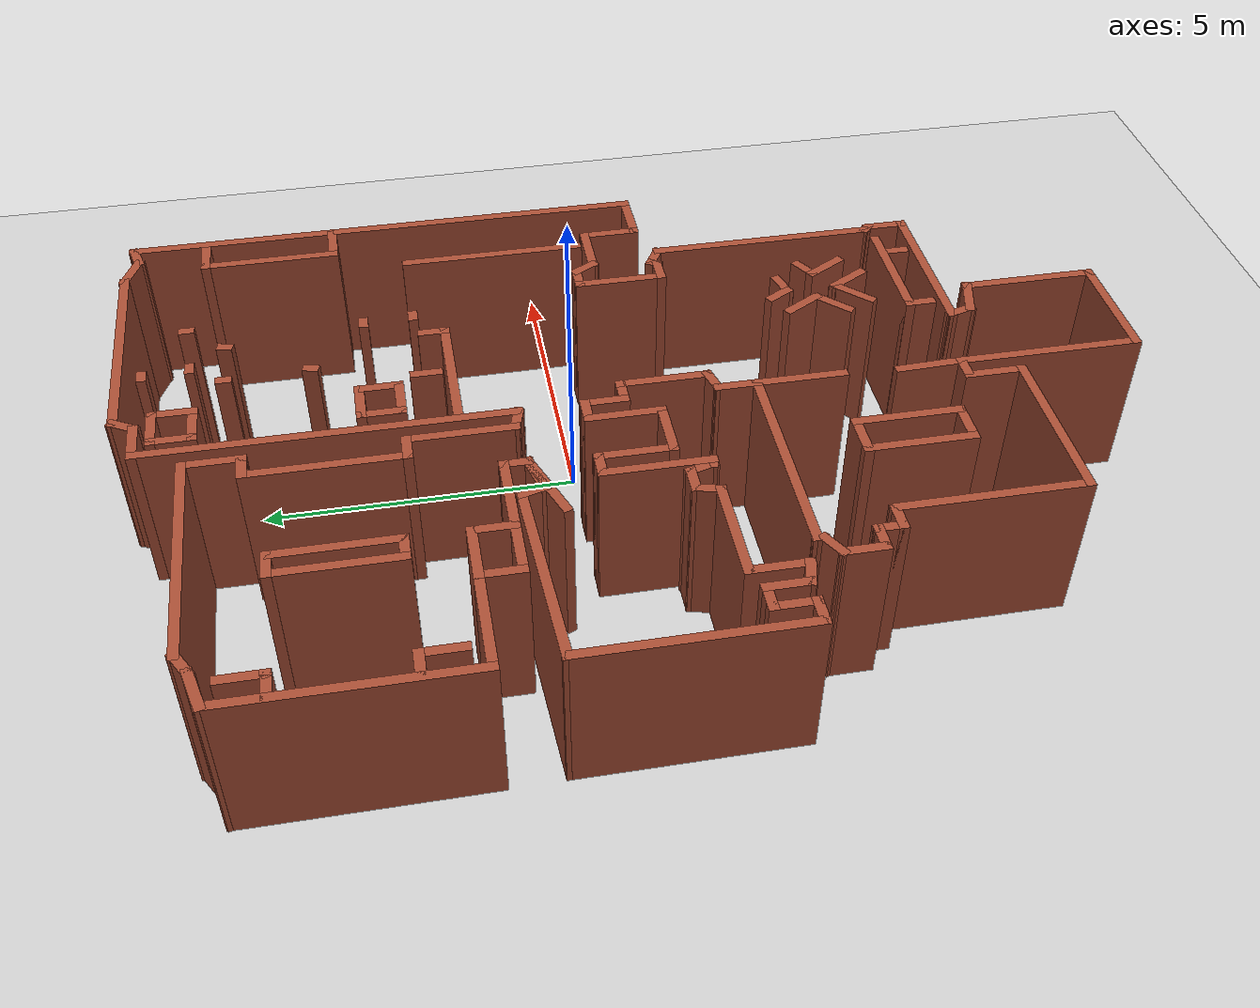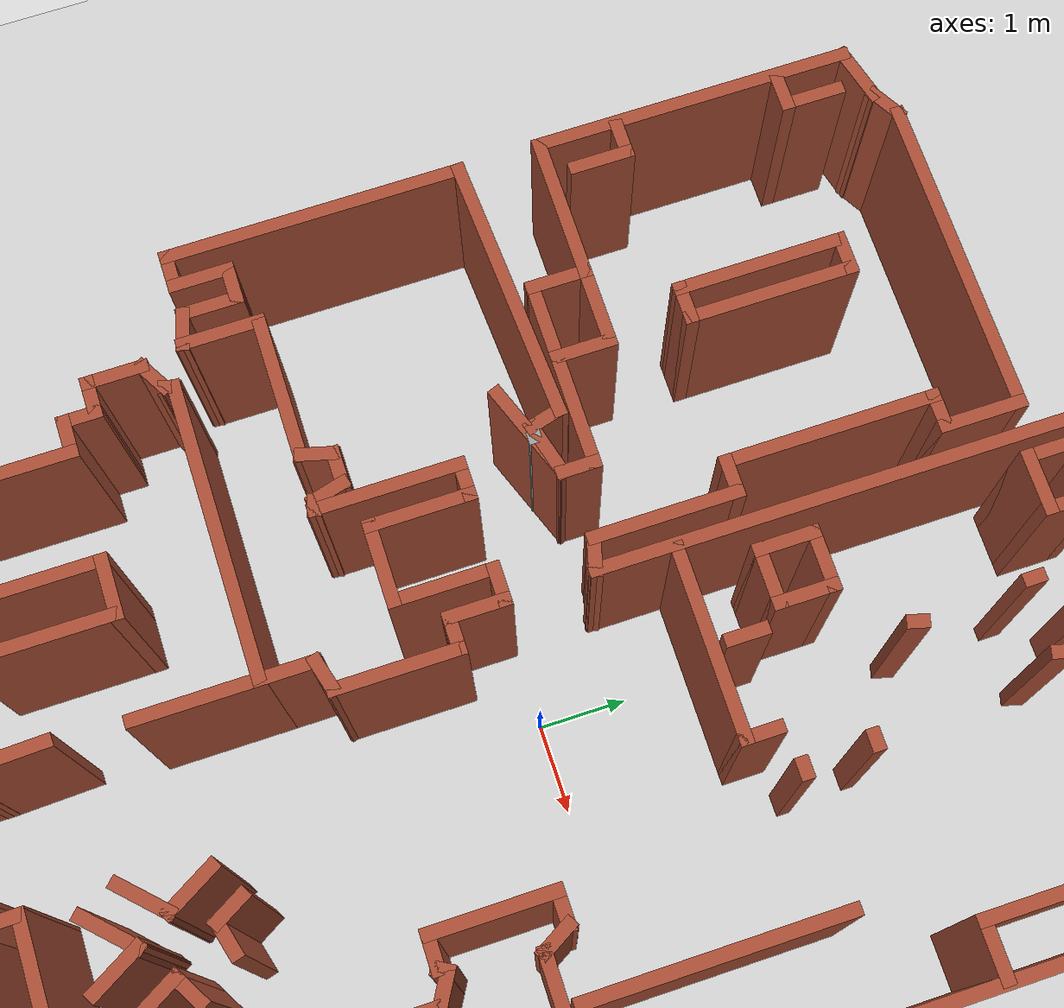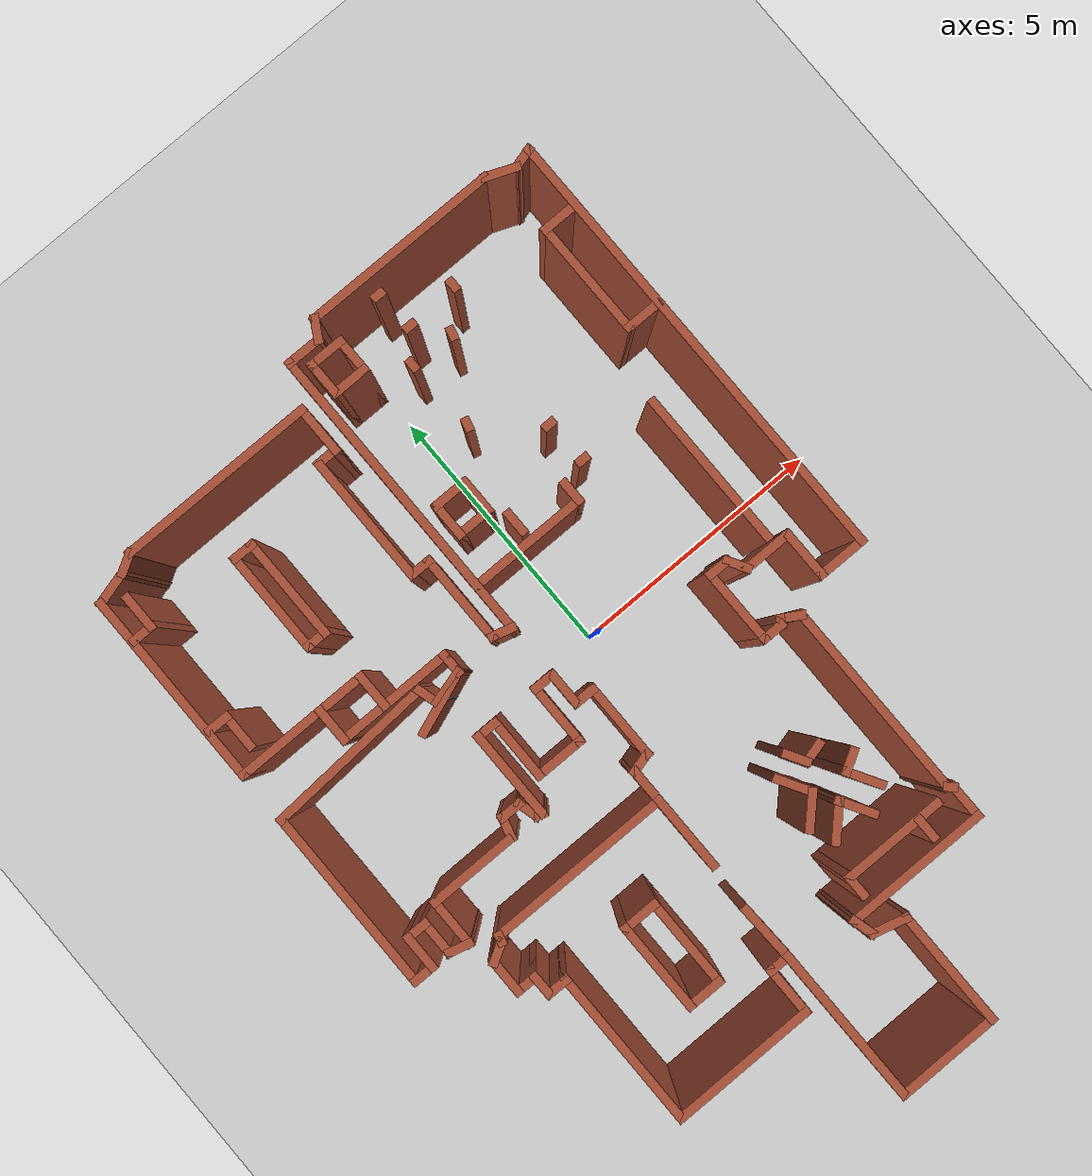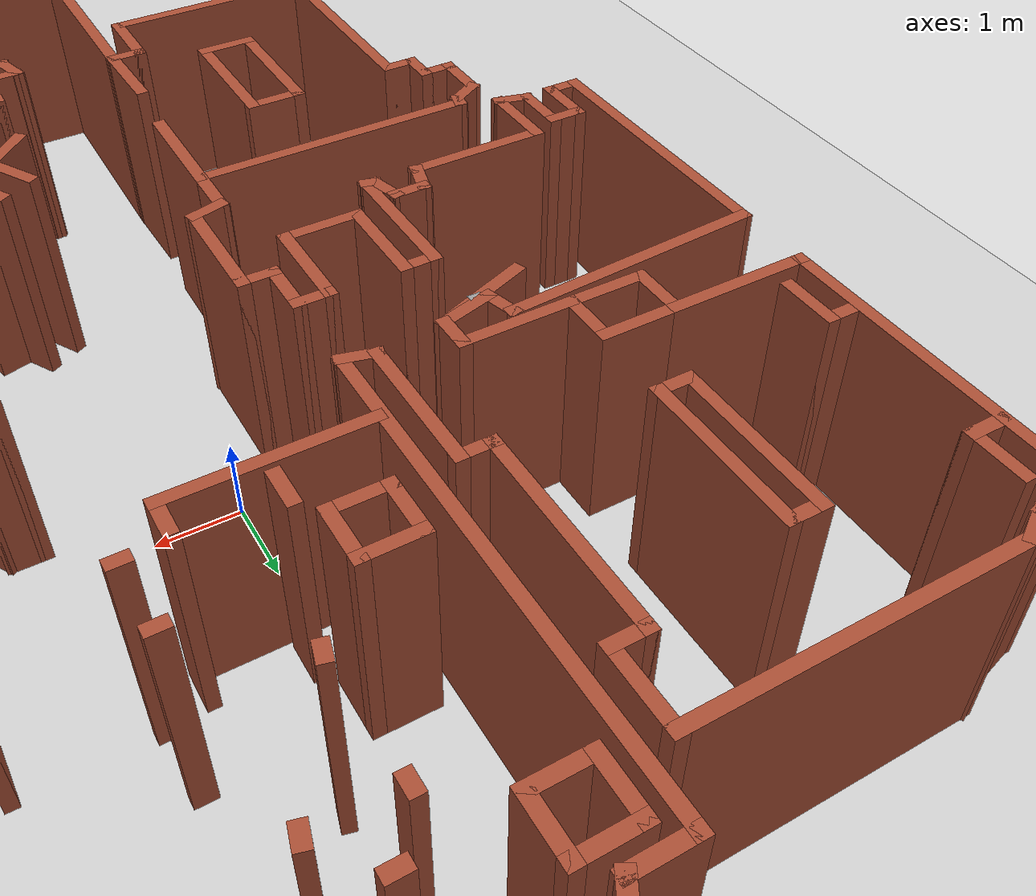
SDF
<sdf version="1.6">
 <world name="default">
  <light name="sun" type="directional">
   <pose>0 0 10 0 -0 0</pose>
   <diffuse>0.8 0.8 0.8 1</diffuse>
   <specular>0.2 0.2 0.2 1</specular>
   <attenuation>
    <range>1000</range>
    <constant>0.9</constant>
    <linear>0.01</linear>
    <quadratic>0.001</quadratic>
   </attenuation>
   <direction>-0.5 0.1 -0.9</direction>
  </light>
  <model name="ground_plane">
   <static>1</static>
   <link name="link">
    <collision name="collision">
     <geometry><plane><normal>0 0 1</normal><size>100 100</size></plane></geometry>
     <surface>
      <contact><collide_bitmask>65535</collide_bitmask></contact>
      <friction><ode><mu>100</mu><mu2>50</mu2></ode></friction>
     </surface>
    </collision>
    <visual name="visual">
     <cast_shadows>0</cast_shadows>
     <geometry><plane><normal>0 0 1</normal><size>100 100</size></plane></geometry>
     <material>
      <script><uri>file://media/materials/scripts/gazebo.material</uri><name>Gazebo/Grey</name></script>
     </material>
    </visual>
   </link>
  </model>
  <gravity>0 0 -9.8</gravity>
  <magnetic_field>6e-06 2.3e-05 -4.2e-05</magnetic_field>
  <atmosphere type="adiabatic"/>
  <physics name="default_physics" default="0" type="ode">
   <max_step_size>0.001</max_step_size>
   <real_time_factor>1</real_time_factor>
   <real_time_update_rate>1000</real_time_update_rate>
  </physics>
  <scene><ambient>0.4 0.4 0.4 1</ambient><background>0.7 0.7 0.7 1</background><shadows>1</shadows></scene>
  <audio><device>default</device></audio>
  <spherical_coordinates>
   <surface_model>EARTH_WGS84</surface_model>
   <latitude_deg>0</latitude_deg>
   <longitude_deg>0</longitude_deg>
   <elevation>0</elevation>
   <heading_deg>0</heading_deg>
  </spherical_coordinates>
  <model name="map_26">
   <pose>-0.762492 -0.95628 0 0 -0 0</pose>
   <link name="Wall_1">
    <collision name="Wall_1_Collision">
     <geometry><box><size>3.75 0.15 2.5</size></box></geometry>
     <pose>0 0 1.25 0 -0 0</pose>
    </collision>
    <visual name="Wall_1_Visual">
     <pose>0 0 1.25 0 -0 0</pose>
     <geometry><box><size>3.75 0.15 2.5</size></box></geometry>
     <material>
      <script><uri>file://media/materials/scripts/gazebo.material</uri><name>Gazebo/Bricks</name></script>
      <ambient>1 1 1 1</ambient>
     </material>
     <meta><layer>0</layer></meta>
    </visual>
    <pose>2.37487 7.7923 0 0 -0 3.14159</pose>
   </link>
   <link name="Wall_10">
    <collision name="Wall_10_Collision">
     <geometry><box><size>1 0.15 2.5</size></box></geometry>
     <pose>0 0 1.25 0 -0 0</pose>
    </collision>
    <visual name="Wall_10_Visual">
     <pose>0 0 1.25 0 -0 0</pose>
     <geometry><box><size>1 0.15 2.5</size></box></geometry>
     <material>
      <script><uri>file://media/materials/scripts/gazebo.material</uri><name>Gazebo/Bricks</name></script>
      <ambient>1 1 1 1</ambient>
     </material>
     <meta><layer>0</layer></meta>
    </visual>
    <pose>-0.538205 6.35478 0 0 -0 1.5708</pose>
   </link>
   <link name="Wall_101">
    <collision name="Wall_101_Collision">
     <geometry><box><size>0.75 0.15 2.5</size></box></geometry>
     <pose>0 0 1.25 0 -0 0</pose>
    </collision>
    <visual name="Wall_101_Visual">
     <pose>0 0 1.25 0 -0 0</pose>
     <geometry><box><size>0.75 0.15 2.5</size></box></geometry>
     <material>
      <script><uri>file://media/materials/scripts/gazebo.material</uri><name>Gazebo/Bricks</name></script>
      <ambient>1 1 1 1</ambient>
     </material>
     <meta><layer>0</layer></meta>
    </visual>
    <pose>-4.63789 5.94255 0 0 -0 -1.5708</pose>
   </link>
   <link name="Wall_102">
    <collision name="Wall_102_Collision">
     <geometry><box><size>0.5 0.15 2.5</size></box></geometry>
     <pose>0 0 1.25 0 -0 0</pose>
    </collision>
    <visual name="Wall_102_Visual">
     <pose>0 0 1.25 0 -0 0</pose>
     <geometry><box><size>0.5 0.15 2.5</size></box></geometry>
     <material>
      <script><uri>file://media/materials/scripts/gazebo.material</uri><name>Gazebo/Bricks</name></script>
      <ambient>1 1 1 1</ambient>
     </material>
     <meta><layer>0</layer></meta>
    </visual>
    <pose>-4.81289 5.64255 0 0 -0 3.14159</pose>
   </link>
   <link name="Wall_106">
    <collision name="Wall_106_Collision">
     <geometry><box><size>0.5 0.15 2.5</size></box></geometry>
     <pose>0 0 1.25 0 -0 0</pose>
    </collision>
    <visual name="Wall_106_Visual">
     <pose>0 0 1.25 0 -0 0</pose>
     <geometry><box><size>0.5 0.15 2.5</size></box></geometry>
     <material>
      <script><uri>file://media/materials/scripts/gazebo.material</uri><name>Gazebo/Bricks</name></script>
      <ambient>1 1 1 1</ambient>
     </material>
     <meta><layer>0</layer></meta>
    </visual>
    <pose>-4.80985 3.74444 0 0 -0 0</pose>
   </link>
   <link name="Wall_107">
    <collision name="Wall_107_Collision">
     <geometry><box><size>0.75 0.15 2.5</size></box></geometry>
     <pose>0 0 1.25 0 -0 0</pose>
    </collision>
    <visual name="Wall_107_Visual">
     <pose>0 0 1.25 0 -0 0</pose>
     <geometry><box><size>0.75 0.15 2.5</size></box></geometry>
     <material>
      <script><uri>file://media/materials/scripts/gazebo.material</uri><name>Gazebo/Bricks</name></script>
      <ambient>1 1 1 1</ambient>
     </material>
     <meta><layer>0</layer></meta>
    </visual>
    <pose>-4.63485 3.44444 0 0 -0 -1.5708</pose>
   </link>
   <link name="Wall_109">
    <collision name="Wall_109_Collision">
     <geometry><box><size>0.5 0.15 2.5</size></box></geometry>
     <pose>0 0 1.25 0 -0 0</pose>
    </collision>
    <visual name="Wall_109_Visual">
     <pose>0 0 1.25 0 -0 0</pose>
     <geometry><box><size>0.5 0.15 2.5</size></box></geometry>
     <material>
      <script><uri>file://media/materials/scripts/gazebo.material</uri><name>Gazebo/Bricks</name></script>
      <ambient>1 1 1 1</ambient>
     </material>
     <meta><layer>0</layer></meta>
    </visual>
    <pose>-2.73114 5.61802 0 0 -0 3.14159</pose>
   </link>
   <link name="Wall_11">
    <collision name="Wall_11_Collision">
     <geometry><box><size>3.75 0.15 2.5</size></box></geometry>
     <pose>0 0 1.25 0 -0 0</pose>
    </collision>
    <visual name="Wall_11_Visual">
     <pose>0 0 1.25 0 -0 0</pose>
     <geometry><box><size>3.75 0.15 2.5</size></box></geometry>
     <material>
      <script><uri>file://media/materials/scripts/gazebo.material</uri><name>Gazebo/Bricks</name></script>
      <ambient>1 1 1 1</ambient>
     </material>
     <meta><layer>0</layer></meta>
    </visual>
    <pose>-2.3382 6.77978 0 0 -0 3.14159</pose>
   </link>
   <link name="Wall_110">
    <collision name="Wall_110_Collision">
     <geometry><box><size>2 0.15 2.5</size></box></geometry>
     <pose>0 0 1.25 0 -0 0</pose>
    </collision>
    <visual name="Wall_110_Visual">
     <pose>0 0 1.25 0 -0 0</pose>
     <geometry><box><size>2 0.15 2.5</size></box></geometry>
     <material>
      <script><uri>file://media/materials/scripts/gazebo.material</uri><name>Gazebo/Bricks</name></script>
      <ambient>1 1 1 1</ambient>
     </material>
     <meta><layer>0</layer></meta>
    </visual>
    <pose>-2.90614 4.69302 0 0 -0 -1.5708</pose>
   </link>
   <link name="Wall_111">
    <collision name="Wall_111_Collision">
     <geometry><box><size>0.5 0.15 2.5</size></box></geometry>
     <pose>0 0 1.25 0 -0 0</pose>
    </collision>
    <visual name="Wall_111_Visual">
     <pose>0 0 1.25 0 -0 0</pose>
     <geometry><box><size>0.5 0.15 2.5</size></box></geometry>
     <material>
      <script><uri>file://media/materials/scripts/gazebo.material</uri><name>Gazebo/Bricks</name></script>
      <ambient>1 1 1 1</ambient>
     </material>
     <meta><layer>0</layer></meta>
    </visual>
    <pose>-2.73114 3.76802 0 0 -0 0</pose>
   </link>
   <link name="Wall_113">
    <collision name="Wall_113_Collision">
     <geometry><box><size>2 0.15 2.5</size></box></geometry>
     <pose>0 0 1.25 0 -0 0</pose>
    </collision>
    <visual name="Wall_113_Visual">
     <pose>0 0 1.25 0 -0 0</pose>
     <geometry><box><size>2 0.15 2.5</size></box></geometry>
     <material>
      <script><uri>file://media/materials/scripts/gazebo.material</uri><name>Gazebo/Bricks</name></script>
      <ambient>1 1 1 1</ambient>
     </material>
     <meta><layer>0</layer></meta>
    </visual>
    <pose>-2.55614 4.69302 0 0 -0 -1.5708</pose>
   </link>
   <link name="Wall_115">
    <collision name="Wall_115_Collision">
     <geometry><box><size>1 0.15 2.5</size></box></geometry>
     <pose>0 0 1.25 0 -0 0</pose>
    </collision>
    <visual name="Wall_115_Visual">
     <pose>0 0 1.25 0 -0 0</pose>
     <geometry><box><size>1 0.15 2.5</size></box></geometry>
     <material>
      <script><uri>file://media/materials/scripts/gazebo.material</uri><name>Gazebo/Bricks</name></script>
      <ambient>1 1 1 1</ambient>
     </material>
     <meta><layer>0</layer></meta>
    </visual>
    <pose>-2.99587 2.84949 0 0 -0 0</pose>
   </link>
   <link name="Wall_116">
    <collision name="Wall_116_Collision">
     <geometry><box><size>0.75 0.15 2.5</size></box></geometry>
     <pose>0 0 1.25 0 -0 0</pose>
    </collision>
    <visual name="Wall_116_Visual">
     <pose>0 0 1.25 0 -0 0</pose>
     <geometry><box><size>0.75 0.15 2.5</size></box></geometry>
     <material>
      <script><uri>file://media/materials/scripts/gazebo.material</uri><name>Gazebo/Bricks</name></script>
      <ambient>1 1 1 1</ambient>
     </material>
     <meta><layer>0</layer></meta>
    </visual>
    <pose>-2.57087 2.54948 0 0 -0 -1.5708</pose>
   </link>
   <link name="Wall_118">
    <collision name="Wall_118_Collision">
     <geometry><box><size>0.75 0.15 2.5</size></box></geometry>
     <pose>0 0 1.25 0 -0 0</pose>
    </collision>
    <visual name="Wall_118_Visual">
     <pose>0 0 1.25 0 -0 0</pose>
     <geometry><box><size>0.75 0.15 2.5</size></box></geometry>
     <material>
      <script><uri>file://media/materials/scripts/gazebo.material</uri><name>Gazebo/Bricks</name></script>
      <ambient>1 1 1 1</ambient>
     </material>
     <meta><layer>0</layer></meta>
    </visual>
    <pose>4.68444 6.49698 0 0 -0 3.14159</pose>
   </link>
   <link name="Wall_119">
    <collision name="Wall_119_Collision">
     <geometry><box><size>2.25 0.15 2.5</size></box></geometry>
     <pose>0 0 1.25 0 -0 0</pose>
    </collision>
    <visual name="Wall_119_Visual">
     <pose>0 0 1.25 0 -0 0</pose>
     <geometry><box><size>2.25 0.15 2.5</size></box></geometry>
     <material>
      <script><uri>file://media/materials/scripts/gazebo.material</uri><name>Gazebo/Bricks</name></script>
      <ambient>1 1 1 1</ambient>
     </material>
     <meta><layer>0</layer></meta>
    </visual>
    <pose>4.38444 5.44698 0 0 -0 -1.5708</pose>
   </link>
   <link name="Wall_12">
    <collision name="Wall_12_Collision">
     <geometry><box><size>0.5 0.15 2.5</size></box></geometry>
     <pose>0 0 1.25 0 -0 0</pose>
    </collision>
    <visual name="Wall_12_Visual">
     <pose>0 0 1.25 0 -0 0</pose>
     <geometry><box><size>0.5 0.15 2.5</size></box></geometry>
     <material>
      <script><uri>file://media/materials/scripts/gazebo.material</uri><name>Gazebo/Bricks</name></script>
      <ambient>1 1 1 1</ambient>
     </material>
     <meta><layer>0</layer></meta>
    </visual>
    <pose>-4.28976 6.69228 0 0 -0 -2.61799</pose>
   </link>
   <link name="Wall_120">
    <collision name="Wall_120_Collision">
     <geometry><box><size>0.75 0.15 2.5</size></box></geometry>
     <pose>0 0 1.25 0 -0 0</pose>
    </collision>
    <visual name="Wall_120_Visual">
     <pose>0 0 1.25 0 -0 0</pose>
     <geometry><box><size>0.75 0.15 2.5</size></box></geometry>
     <material>
      <script><uri>file://media/materials/scripts/gazebo.material</uri><name>Gazebo/Bricks</name></script>
      <ambient>1 1 1 1</ambient>
     </material>
     <meta><layer>0</layer></meta>
    </visual>
    <pose>4.68444 4.39698 0 0 -0 0</pose>
   </link>
   <link name="Wall_122">
    <collision name="Wall_122_Collision">
     <geometry><box><size>2.25 0.15 2.5</size></box></geometry>
     <pose>0 0 1.25 0 -0 0</pose>
    </collision>
    <visual name="Wall_122_Visual">
     <pose>0 0 1.25 0 -0 0</pose>
     <geometry><box><size>2.25 0.15 2.5</size></box></geometry>
     <material>
      <script><uri>file://media/materials/scripts/gazebo.material</uri><name>Gazebo/Bricks</name></script>
      <ambient>1 1 1 1</ambient>
     </material>
     <meta><layer>0</layer></meta>
    </visual>
    <pose>0.899445 2.77296 0 0 -0 0</pose>
   </link>
   <link name="Wall_123">
    <collision name="Wall_123_Collision">
     <geometry><box><size>0.5 0.15 2.5</size></box></geometry>
     <pose>0 0 1.25 0 -0 0</pose>
    </collision>
    <visual name="Wall_123_Visual">
     <pose>0 0 1.25 0 -0 0</pose>
     <geometry><box><size>0.5 0.15 2.5</size></box></geometry>
     <material>
      <script><uri>file://media/materials/scripts/gazebo.material</uri><name>Gazebo/Bricks</name></script>
      <ambient>1 1 1 1</ambient>
     </material>
     <meta><layer>0</layer></meta>
    </visual>
    <pose>1.94945 2.94796 0 0 -0 1.5708</pose>
   </link>
   <link name="Wall_125">
    <collision name="Wall_125_Collision">
     <geometry><box><size>0.5 0.15 2.5</size></box></geometry>
     <pose>0 0 1.25 0 -0 0</pose>
    </collision>
    <visual name="Wall_125_Visual">
     <pose>0 0 1.25 0 -0 0</pose>
     <geometry><box><size>0.5 0.15 2.5</size></box></geometry>
     <material>
      <script><uri>file://media/materials/scripts/gazebo.material</uri><name>Gazebo/Bricks</name></script>
      <ambient>1 1 1 1</ambient>
     </material>
     <meta><layer>0</layer></meta>
    </visual>
    <pose>0.936584 3.15309 0 0 -0 -1.5708</pose>
   </link>
   <link name="Wall_128">
    <collision name="Wall_128_Collision">
     <geometry><box><size>0.75 0.15 2.5</size></box></geometry>
     <pose>0 0 1.25 0 -0 0</pose>
    </collision>
    <visual name="Wall_128_Visual">
     <pose>0 0 1.25 0 -0 0</pose>
     <geometry><box><size>0.75 0.15 2.5</size></box></geometry>
     <material>
      <script><uri>file://media/materials/scripts/gazebo.material</uri><name>Gazebo/Bricks</name></script>
      <ambient>1 1 1 1</ambient>
     </material>
     <meta><layer>0</layer></meta>
    </visual>
    <pose>0.057621 6.93716 0 0 -0 -1.5708</pose>
   </link>
   <link name="Wall_129">
    <collision name="Wall_129_Collision">
     <geometry><box><size>0.75 0.15 2.5</size></box></geometry>
     <pose>0 0 1.25 0 -0 0</pose>
    </collision>
    <visual name="Wall_129_Visual">
     <pose>0 0 1.25 0 -0 0</pose>
     <geometry><box><size>0.75 0.15 2.5</size></box></geometry>
     <material>
      <script><uri>file://media/materials/scripts/gazebo.material</uri><name>Gazebo/Bricks</name></script>
      <ambient>1 1 1 1</ambient>
     </material>
     <meta><layer>0</layer></meta>
    </visual>
    <pose>0.357621 6.63716 0 0 -0 0</pose>
   </link>
   <link name="Wall_13">
    <collision name="Wall_13_Collision">
     <geometry><box><size>0.75 0.15 2.5</size></box></geometry>
     <pose>0 0 1.25 0 -0 0</pose>
    </collision>
    <visual name="Wall_13_Visual">
     <pose>0 0 1.25 0 -0 0</pose>
     <geometry><box><size>0.75 0.15 2.5</size></box></geometry>
     <material>
      <script><uri>file://media/materials/scripts/gazebo.material</uri><name>Gazebo/Bricks</name></script>
      <ambient>1 1 1 1</ambient>
     </material>
     <meta><layer>0</layer></meta>
    </visual>
    <pose>-4.73109 6.52713 0 0 -0 -2.87979</pose>
   </link>
   <link name="Wall_130">
    <collision name="Wall_130_Collision">
     <geometry><box><size>0.75 0.15 2.5</size></box></geometry>
     <pose>0 0 1.25 0 -0 0</pose>
    </collision>
    <visual name="Wall_130_Visual">
     <pose>0 0 1.25 0 -0 0</pose>
     <geometry><box><size>0.75 0.15 2.5</size></box></geometry>
     <material>
      <script><uri>file://media/materials/scripts/gazebo.material</uri><name>Gazebo/Bricks</name></script>
      <ambient>1 1 1 1</ambient>
     </material>
     <meta><layer>0</layer></meta>
    </visual>
    <pose>0.657621 6.93716 0 0 -0 1.5708</pose>
   </link>
   <link name="Wall_131">
    <collision name="Wall_131_Collision">
     <geometry><box><size>0.75 0.15 2.5</size></box></geometry>
     <pose>0 0 1.25 0 -0 0</pose>
    </collision>
    <visual name="Wall_131_Visual">
     <pose>0 0 1.25 0 -0 0</pose>
     <geometry><box><size>0.75 0.15 2.5</size></box></geometry>
     <material>
      <script><uri>file://media/materials/scripts/gazebo.material</uri><name>Gazebo/Bricks</name></script>
      <ambient>1 1 1 1</ambient>
     </material>
     <meta><layer>0</layer></meta>
    </visual>
    <pose>0.357621 7.23716 0 0 -0 3.14159</pose>
   </link>
   <link name="Wall_135">
    <collision name="Wall_135_Collision">
     <geometry><box><size>0.75 0.15 2.5</size></box></geometry>
     <pose>0 0 1.25 0 -0 0</pose>
    </collision>
    <visual name="Wall_135_Visual">
     <pose>0 0 1.25 0 -0 0</pose>
     <geometry><box><size>0.75 0.15 2.5</size></box></geometry>
     <material>
      <script><uri>file://media/materials/scripts/gazebo.material</uri><name>Gazebo/Bricks</name></script>
      <ambient>1 1 1 1</ambient>
     </material>
     <meta><layer>0</layer></meta>
    </visual>
    <pose>0.127013 3.88392 0 0 -0 -1.5708</pose>
   </link>
   <link name="Wall_136">
    <collision name="Wall_136_Collision">
     <geometry><box><size>0.75 0.15 2.5</size></box></geometry>
     <pose>0 0 1.25 0 -0 0</pose>
    </collision>
    <visual name="Wall_136_Visual">
     <pose>0 0 1.25 0 -0 0</pose>
     <geometry><box><size>0.75 0.15 2.5</size></box></geometry>
     <material>
      <script><uri>file://media/materials/scripts/gazebo.material</uri><name>Gazebo/Bricks</name></script>
      <ambient>1 1 1 1</ambient>
     </material>
     <meta><layer>0</layer></meta>
    </visual>
    <pose>0.427013 3.58392 0 0 -0 0</pose>
   </link>
   <link name="Wall_137">
    <collision name="Wall_137_Collision">
     <geometry><box><size>0.75 0.15 2.5</size></box></geometry>
     <pose>0 0 1.25 0 -0 0</pose>
    </collision>
    <visual name="Wall_137_Visual">
     <pose>0 0 1.25 0 -0 0</pose>
     <geometry><box><size>0.75 0.15 2.5</size></box></geometry>
     <material>
      <script><uri>file://media/materials/scripts/gazebo.material</uri><name>Gazebo/Bricks</name></script>
      <ambient>1 1 1 1</ambient>
     </material>
     <meta><layer>0</layer></meta>
    </visual>
    <pose>0.727013 3.88392 0 0 -0 1.5708</pose>
   </link>
   <link name="Wall_138">
    <collision name="Wall_138_Collision">
     <geometry><box><size>0.75 0.15 2.5</size></box></geometry>
     <pose>0 0 1.25 0 -0 0</pose>
    </collision>
    <visual name="Wall_138_Visual">
     <pose>0 0 1.25 0 -0 0</pose>
     <geometry><box><size>0.75 0.15 2.5</size></box></geometry>
     <material>
      <script><uri>file://media/materials/scripts/gazebo.material</uri><name>Gazebo/Bricks</name></script>
      <ambient>1 1 1 1</ambient>
     </material>
     <meta><layer>0</layer></meta>
    </visual>
    <pose>0.427013 4.18392 0 0 -0 3.14159</pose>
   </link>
   <link name="Wall_14">
    <collision name="Wall_14_Collision">
     <geometry><box><size>3.75 0.15 2.5</size></box></geometry>
     <pose>0 0 1.25 0 -0 0</pose>
    </collision>
    <visual name="Wall_14_Visual">
     <pose>0 0 1.25 0 -0 0</pose>
     <geometry><box><size>3.75 0.15 2.5</size></box></geometry>
     <material>
      <script><uri>file://media/materials/scripts/gazebo.material</uri><name>Gazebo/Bricks</name></script>
      <ambient>1 1 1 1</ambient>
     </material>
     <meta><layer>0</layer></meta>
    </visual>
    <pose>-5.02087 4.64949 0 0 -0 -1.5708</pose>
   </link>
   <link name="Wall_140">
    <collision name="Wall_140_Collision">
     <geometry><box><size>3 0.15 2.5</size></box></geometry>
     <pose>0 0 1.25 0 -0 0</pose>
    </collision>
    <visual name="Wall_140_Visual">
     <pose>0 0 1.25 0 -0 0</pose>
     <geometry><box><size>3 0.15 2.5</size></box></geometry>
     <material>
      <script><uri>file://media/materials/scripts/gazebo.material</uri><name>Gazebo/Bricks</name></script>
      <ambient>1 1 1 1</ambient>
     </material>
     <meta><layer>0</layer></meta>
    </visual>
    <pose>3.8973 1.78744 0 0 -0 -1.5708</pose>
   </link>
   <link name="Wall_147">
    <collision name="Wall_147_Collision">
     <geometry><box><size>1.75 0.15 2.5</size></box></geometry>
     <pose>0 0 1.25 0 -0 0</pose>
    </collision>
    <visual name="Wall_147_Visual">
     <pose>0 0 1.25 0 -0 0</pose>
     <geometry><box><size>1.75 0.15 2.5</size></box></geometry>
     <material>
      <script><uri>file://media/materials/scripts/gazebo.material</uri><name>Gazebo/Bricks</name></script>
      <ambient>1 1 1 1</ambient>
     </material>
     <meta><layer>0</layer></meta>
    </visual>
    <pose>-1.90848 -3.76343 0 0 -0 -1.5708</pose>
   </link>
   <link name="Wall_148">
    <collision name="Wall_148_Collision">
     <geometry><box><size>0.75 0.15 2.5</size></box></geometry>
     <pose>0 0 1.25 0 -0 0</pose>
    </collision>
    <visual name="Wall_148_Visual">
     <pose>0 0 1.25 0 -0 0</pose>
     <geometry><box><size>0.75 0.15 2.5</size></box></geometry>
     <material>
      <script><uri>file://media/materials/scripts/gazebo.material</uri><name>Gazebo/Bricks</name></script>
      <ambient>1 1 1 1</ambient>
     </material>
     <meta><layer>0</layer></meta>
    </visual>
    <pose>-1.60848 -4.56343 0 0 -0 0</pose>
   </link>
   <link name="Wall_149">
    <collision name="Wall_149_Collision">
     <geometry><box><size>1.75 0.15 2.5</size></box></geometry>
     <pose>0 0 1.25 0 -0 0</pose>
    </collision>
    <visual name="Wall_149_Visual">
     <pose>0 0 1.25 0 -0 0</pose>
     <geometry><box><size>1.75 0.15 2.5</size></box></geometry>
     <material>
      <script><uri>file://media/materials/scripts/gazebo.material</uri><name>Gazebo/Bricks</name></script>
      <ambient>1 1 1 1</ambient>
     </material>
     <meta><layer>0</layer></meta>
    </visual>
    <pose>-1.30848 -3.76343 0 0 -0 1.5708</pose>
   </link>
   <link name="Wall_15">
    <collision name="Wall_15_Collision">
     <geometry><box><size>1.75 0.15 2.5</size></box></geometry>
     <pose>0 0 1.25 0 -0 0</pose>
    </collision>
    <visual name="Wall_15_Visual">
     <pose>0 0 1.25 0 -0 0</pose>
     <geometry><box><size>1.75 0.15 2.5</size></box></geometry>
     <material>
      <script><uri>file://media/materials/scripts/gazebo.material</uri><name>Gazebo/Bricks</name></script>
      <ambient>1 1 1 1</ambient>
     </material>
     <meta><layer>0</layer></meta>
    </visual>
    <pose>-4.22087 2.84949 0 0 -0 0</pose>
   </link>
   <link name="Wall_150">
    <collision name="Wall_150_Collision">
     <geometry><box><size>0.75 0.15 2.5</size></box></geometry>
     <pose>0 0 1.25 0 -0 0</pose>
    </collision>
    <visual name="Wall_150_Visual">
     <pose>0 0 1.25 0 -0 0</pose>
     <geometry><box><size>0.75 0.15 2.5</size></box></geometry>
     <material>
      <script><uri>file://media/materials/scripts/gazebo.material</uri><name>Gazebo/Bricks</name></script>
      <ambient>1 1 1 1</ambient>
     </material>
     <meta><layer>0</layer></meta>
    </visual>
    <pose>-1.60848 -2.96343 0 0 -0 -3.14159</pose>
   </link>
   <link name="Wall_152">
    <collision name="Wall_152_Collision">
     <geometry><box><size>1.5 0.15 2.5</size></box></geometry>
     <pose>0 0 1.25 0 -0 0</pose>
    </collision>
    <visual name="Wall_152_Visual">
     <pose>0 0 1.25 0 -0 0</pose>
     <geometry><box><size>1.5 0.15 2.5</size></box></geometry>
     <material>
      <script><uri>file://media/materials/scripts/gazebo.material</uri><name>Gazebo/Bricks</name></script>
      <ambient>1 1 1 1</ambient>
     </material>
     <meta><layer>0</layer></meta>
    </visual>
    <pose>-0.181178 -2.42316 0 0 -0 -1.5708</pose>
   </link>
   <link name="Wall_154">
    <collision name="Wall_154_Collision">
     <geometry><box><size>1.13912 0.15 2.5</size></box></geometry>
     <pose>0 0 1.25 0 -0 0</pose>
    </collision>
    <visual name="Wall_154_Visual">
     <pose>0 0 1.25 0 -0 0</pose>
     <geometry><box><size>1.13912 0.15 2.5</size></box></geometry>
     <material>
      <script><uri>file://media/materials/scripts/gazebo.material</uri><name>Gazebo/Bricks</name></script>
      <ambient>1 1 1 1</ambient>
     </material>
     <meta><layer>0</layer></meta>
    </visual>
    <pose>-0.226623 -4.47546 0 0 -0 -1.53752</pose>
   </link>
   <link name="Wall_156">
    <collision name="Wall_156_Collision">
     <geometry><box><size>2 0.15 2.5</size></box></geometry>
     <pose>0 0 1.25 0 -0 0</pose>
    </collision>
    <visual name="Wall_156_Visual">
     <pose>0 0 1.25 0 -0 0</pose>
     <geometry><box><size>2 0.15 2.5</size></box></geometry>
     <material>
      <script><uri>file://media/materials/scripts/gazebo.material</uri><name>Gazebo/Bricks</name></script>
      <ambient>1 1 1 1</ambient>
     </material>
     <meta><layer>0</layer></meta>
    </visual>
    <pose>2.27793 -4.65197 0 0 -0 0</pose>
   </link>
   <link name="Wall_160">
    <collision name="Wall_160_Collision">
     <geometry><box><size>0.5 0.15 2.5</size></box></geometry>
     <pose>0 0 1.25 0 -0 0</pose>
    </collision>
    <visual name="Wall_160_Visual">
     <pose>0 0 1.25 0 -0 0</pose>
     <geometry><box><size>0.5 0.15 2.5</size></box></geometry>
     <material>
      <script><uri>file://media/materials/scripts/gazebo.material</uri><name>Gazebo/Bricks</name></script>
      <ambient>1 1 1 1</ambient>
     </material>
     <meta><layer>0</layer></meta>
    </visual>
    <pose>1.35293 -4.82697 0 0 -0 -1.5708</pose>
   </link>
   <link name="Wall_162">
    <collision name="Wall_162_Collision">
     <geometry><box><size>0.5 0.15 2.5</size></box></geometry>
     <pose>0 0 1.25 0 -0 0</pose>
    </collision>
    <visual name="Wall_162_Visual">
     <pose>0 0 1.25 0 -0 0</pose>
     <geometry><box><size>0.5 0.15 2.5</size></box></geometry>
     <material>
      <script><uri>file://media/materials/scripts/gazebo.material</uri><name>Gazebo/Bricks</name></script>
      <ambient>1 1 1 1</ambient>
     </material>
     <meta><layer>0</layer></meta>
    </visual>
    <pose>2.81016 -4.8501 0 0 -0 -1.5708</pose>
   </link>
   <link name="Wall_164">
    <collision name="Wall_164_Collision">
     <geometry><box><size>0.5 0.15 2.5</size></box></geometry>
     <pose>0 0 1.25 0 -0 0</pose>
    </collision>
    <visual name="Wall_164_Visual">
     <pose>0 0 1.25 0 -0 0</pose>
     <geometry><box><size>0.5 0.15 2.5</size></box></geometry>
     <material>
      <script><uri>file://media/materials/scripts/gazebo.material</uri><name>Gazebo/Bricks</name></script>
      <ambient>1 1 1 1</ambient>
     </material>
     <meta><layer>0</layer></meta>
    </visual>
    <pose>1.94931 -2.65238 0 0 -0 -1.0472</pose>
   </link>
   <link name="Wall_165">
    <collision name="Wall_165_Collision">
     <geometry><box><size>0.5 0.15 2.5</size></box></geometry>
     <pose>0 0 1.25 0 -0 0</pose>
    </collision>
    <visual name="Wall_165_Visual">
     <pose>0 0 1.25 0 -0 0</pose>
     <geometry><box><size>0.5 0.15 2.5</size></box></geometry>
     <material>
      <script><uri>file://media/materials/scripts/gazebo.material</uri><name>Gazebo/Bricks</name></script>
      <ambient>1 1 1 1</ambient>
     </material>
     <meta><layer>0</layer></meta>
    </visual>
    <pose>2.20585 -2.75864 0 0 -0 0.261799</pose>
   </link>
   <link name="Wall_167">
    <collision name="Wall_167_Collision">
     <geometry><box><size>0.75 0.15 2.5</size></box></geometry>
     <pose>0 0 1.25 0 -0 0</pose>
    </collision>
    <visual name="Wall_167_Visual">
     <pose>0 0 1.25 0 -0 0</pose>
     <geometry><box><size>0.75 0.15 2.5</size></box></geometry>
     <material>
      <script><uri>file://media/materials/scripts/gazebo.material</uri><name>Gazebo/Bricks</name></script>
      <ambient>1 1 1 1</ambient>
     </material>
     <meta><layer>0</layer></meta>
    </visual>
    <pose>1.64172 -2.96881 0 0 -0 -1.0472</pose>
   </link>
   <link name="Wall_173">
    <collision name="Wall_173_Collision">
     <geometry><box><size>0.75 0.15 2.5</size></box></geometry>
     <pose>0 0 1.25 0 -0 0</pose>
    </collision>
    <visual name="Wall_173_Visual">
     <pose>0 0 1.25 0 -0 0</pose>
     <geometry><box><size>0.75 0.15 2.5</size></box></geometry>
     <material>
      <script><uri>file://media/materials/scripts/gazebo.material</uri><name>Gazebo/Bricks</name></script>
      <ambient>1 1 1 1</ambient>
     </material>
     <meta><layer>0</layer></meta>
    </visual>
    <pose>1.57959 -3.44075 0 0 -0 -2.35619</pose>
   </link>
   <link name="Wall_178">
    <collision name="Wall_178_Collision">
     <geometry><box><size>0.5 0.15 2.5</size></box></geometry>
     <pose>0 0 1.25 0 -0 0</pose>
    </collision>
    <visual name="Wall_178_Visual">
     <pose>0 0 1.25 0 -0 0</pose>
     <geometry><box><size>0.5 0.15 2.5</size></box></geometry>
     <material>
      <script><uri>file://media/materials/scripts/gazebo.material</uri><name>Gazebo/Bricks</name></script>
      <ambient>1 1 1 1</ambient>
     </material>
     <meta><layer>0</layer></meta>
    </visual>
    <pose>2.5685 -3.24602 0 0 -0 0.523599</pose>
   </link>
   <link name="Wall_180">
    <collision name="Wall_180_Collision">
     <geometry><box><size>0.75 0.15 2.5</size></box></geometry>
     <pose>0 0 1.25 0 -0 0</pose>
    </collision>
    <visual name="Wall_180_Visual">
     <pose>0 0 1.25 0 -0 0</pose>
     <geometry><box><size>0.75 0.15 2.5</size></box></geometry>
     <material>
      <script><uri>file://media/materials/scripts/gazebo.material</uri><name>Gazebo/Bricks</name></script>
      <ambient>1 1 1 1</ambient>
     </material>
     <meta><layer>0</layer></meta>
    </visual>
    <pose>2.56694 -3.59333 0 0 -0 -1.0472</pose>
   </link>
   <link name="Wall_182">
    <collision name="Wall_182_Collision">
     <geometry><box><size>0.75 0.15 2.5</size></box></geometry>
     <pose>0 0 1.25 0 -0 0</pose>
    </collision>
    <visual name="Wall_182_Visual">
     <pose>0 0 1.25 0 -0 0</pose>
     <geometry><box><size>0.75 0.15 2.5</size></box></geometry>
     <material>
      <script><uri>file://media/materials/scripts/gazebo.material</uri><name>Gazebo/Bricks</name></script>
      <ambient>1 1 1 1</ambient>
     </material>
     <meta><layer>0</layer></meta>
    </visual>
    <pose>2.17372 -3.8709 0 0 -0 -1.0472</pose>
   </link>
   <link name="Wall_184">
    <collision name="Wall_184_Collision">
     <geometry><box><size>0.804232 0.15 2.5</size></box></geometry>
     <pose>0 0 1.25 0 -0 0</pose>
    </collision>
    <visual name="Wall_184_Visual">
     <pose>0 0 1.25 0 -0 0</pose>
     <geometry><box><size>0.804232 0.15 2.5</size></box></geometry>
     <material>
      <script><uri>file://media/materials/scripts/gazebo.material</uri><name>Gazebo/Bricks</name></script>
      <ambient>1 1 1 1</ambient>
     </material>
     <meta><layer>0</layer></meta>
    </visual>
    <pose>1.79242 -3.8424 0 0 -0 0.785398</pose>
   </link>
   <link name="Wall_186">
    <collision name="Wall_186_Collision">
     <geometry><box><size>0.25 0.15 2.5</size></box></geometry>
     <pose>0 0 1.25 0 -0 0</pose>
    </collision>
    <visual name="Wall_186_Visual">
     <pose>0 0 1.25 0 -0 0</pose>
     <geometry><box><size>0.25 0.15 2.5</size></box></geometry>
     <material>
      <script><uri>file://media/materials/scripts/gazebo.material</uri><name>Gazebo/Bricks</name></script>
      <ambient>1 1 1 1</ambient>
     </material>
     <meta><layer>0</layer></meta>
    </visual>
    <pose>1.61111 7.42221 0 0 -0 0</pose>
   </link>
   <link name="Wall_188">
    <collision name="Wall_188_Collision">
     <geometry><box><size>0.25 0.15 2.5</size></box></geometry>
     <pose>0 0 1.25 0 -0 0</pose>
    </collision>
    <visual name="Wall_188_Visual">
     <pose>0 0 1.25 0 -0 0</pose>
     <geometry><box><size>0.25 0.15 2.5</size></box></geometry>
     <material>
      <script><uri>file://media/materials/scripts/gazebo.material</uri><name>Gazebo/Bricks</name></script>
      <ambient>1 1 1 1</ambient>
     </material>
     <meta><layer>0</layer></meta>
    </visual>
    <pose>1.6805 6.70516 0 0 -0 0</pose>
   </link>
   <link name="Wall_19">
    <collision name="Wall_19_Collision">
     <geometry><box><size>0.75 0.15 2.5</size></box></geometry>
     <pose>0 0 1.25 0 -0 0</pose>
    </collision>
    <visual name="Wall_19_Visual">
     <pose>0 0 1.25 0 -0 0</pose>
     <geometry><box><size>0.75 0.15 2.5</size></box></geometry>
     <material>
      <script><uri>file://media/materials/scripts/gazebo.material</uri><name>Gazebo/Bricks</name></script>
      <ambient>1 1 1 1</ambient>
     </material>
     <meta><layer>0</layer></meta>
    </visual>
    <pose>-3.42087 2.54948 0 0 -0 -1.5708</pose>
   </link>
   <link name="Wall_192">
    <collision name="Wall_192_Collision">
     <geometry><box><size>0.25 0.15 2.5</size></box></geometry>
     <pose>0 0 1.25 0 -0 0</pose>
    </collision>
    <visual name="Wall_192_Visual">
     <pose>0 0 1.25 0 -0 0</pose>
     <geometry><box><size>0.25 0.15 2.5</size></box></geometry>
     <material>
      <script><uri>file://media/materials/scripts/gazebo.material</uri><name>Gazebo/Bricks</name></script>
      <ambient>1 1 1 1</ambient>
     </material>
     <meta><layer>0</layer></meta>
    </visual>
    <pose>1.30667 6.19255 0 0 -0 -1.5708</pose>
   </link>
   <link name="Wall_194">
    <collision name="Wall_194_Collision">
     <geometry><box><size>0.25 0.15 2.5</size></box></geometry>
     <pose>0 0 1.25 0 -0 0</pose>
    </collision>
    <visual name="Wall_194_Visual">
     <pose>0 0 1.25 0 -0 0</pose>
     <geometry><box><size>0.25 0.15 2.5</size></box></geometry>
     <material>
      <script><uri>file://media/materials/scripts/gazebo.material</uri><name>Gazebo/Bricks</name></script>
      <ambient>1 1 1 1</ambient>
     </material>
     <meta><layer>0</layer></meta>
    </visual>
    <pose>1.36312 4.87581 0 0 -0 -1.8326</pose>
   </link>
   <link name="Wall_196">
    <collision name="Wall_196_Collision">
     <geometry><box><size>0.25 0.15 2.5</size></box></geometry>
     <pose>0 0 1.25 0 -0 0</pose>
    </collision>
    <visual name="Wall_196_Visual">
     <pose>0 0 1.25 0 -0 0</pose>
     <geometry><box><size>0.25 0.15 2.5</size></box></geometry>
     <material>
      <script><uri>file://media/materials/scripts/gazebo.material</uri><name>Gazebo/Bricks</name></script>
      <ambient>1 1 1 1</ambient>
     </material>
     <meta><layer>0</layer></meta>
    </visual>
    <pose>2.37442 4.02201 0 0 -0 0</pose>
   </link>
   <link name="Wall_198">
    <collision name="Wall_198_Collision">
     <geometry><box><size>0.25 0.15 2.5</size></box></geometry>
     <pose>0 0 1.25 0 -0 0</pose>
    </collision>
    <visual name="Wall_198_Visual">
     <pose>0 0 1.25 0 -0 0</pose>
     <geometry><box><size>0.25 0.15 2.5</size></box></geometry>
     <material>
      <script><uri>file://media/materials/scripts/gazebo.material</uri><name>Gazebo/Bricks</name></script>
      <ambient>1 1 1 1</ambient>
     </material>
     <meta><layer>0</layer></meta>
    </visual>
    <pose>2.42068 3.23557 0 0 -0 0</pose>
   </link>
   <link name="Wall_2">
    <collision name="Wall_2_Collision">
     <geometry><box><size>0.5 0.15 2.5</size></box></geometry>
     <pose>0 0 1.25 0 -0 0</pose>
    </collision>
    <visual name="Wall_2_Visual">
     <pose>0 0 1.25 0 -0 0</pose>
     <geometry><box><size>0.5 0.15 2.5</size></box></geometry>
     <material>
      <script><uri>file://media/materials/scripts/gazebo.material</uri><name>Gazebo/Bricks</name></script>
      <ambient>1 1 1 1</ambient>
     </material>
     <meta><layer>0</layer></meta>
    </visual>
    <pose>0.487369 7.64074 0 0 -0 -2.0944</pose>
   </link>
   <link name="Wall_200">
    <collision name="Wall_200_Collision">
     <geometry><box><size>0.25 0.15 2.5</size></box></geometry>
     <pose>0 0 1.25 0 -0 0</pose>
    </collision>
    <visual name="Wall_200_Visual">
     <pose>0 0 1.25 0 -0 0</pose>
     <geometry><box><size>0.25 0.15 2.5</size></box></geometry>
     <material>
      <script><uri>file://media/materials/scripts/gazebo.material</uri><name>Gazebo/Bricks</name></script>
      <ambient>1 1 1 1</ambient>
     </material>
     <meta><layer>0</layer></meta>
    </visual>
    <pose>2.64825 6.77081 0 0 -0 -1.5708</pose>
   </link>
   <link name="Wall_202">
    <collision name="Wall_202_Collision">
     <geometry><box><size>0.25 0.15 2.5</size></box></geometry>
     <pose>0 0 1.25 0 -0 0</pose>
    </collision>
    <visual name="Wall_202_Visual">
     <pose>0 0 1.25 0 -0 0</pose>
     <geometry><box><size>0.25 0.15 2.5</size></box></geometry>
     <material>
      <script><uri>file://media/materials/scripts/gazebo.material</uri><name>Gazebo/Bricks</name></script>
      <ambient>1 1 1 1</ambient>
     </material>
     <meta><layer>0</layer></meta>
    </visual>
    <pose>2.12643 6.17112 0 0 -0 -1.8326</pose>
   </link>
   <link name="Wall_208">
    <collision name="Wall_208_Collision">
     <geometry><box><size>0.5 0.15 2.5</size></box></geometry>
     <pose>0 0 1.25 0 -0 0</pose>
    </collision>
    <visual name="Wall_208_Visual">
     <pose>0 0 1.25 0 -0 0</pose>
     <geometry><box><size>0.5 0.15 2.5</size></box></geometry>
     <material>
      <script><uri>file://media/materials/scripts/gazebo.material</uri><name>Gazebo/Bricks</name></script>
      <ambient>1 1 1 1</ambient>
     </material>
     <meta><layer>0</layer></meta>
    </visual>
    <pose>-1.32087 2.07449 0 0 -0 -1.5708</pose>
   </link>
   <link name="Wall_209">
    <collision name="Wall_209_Collision">
     <geometry><box><size>0.75 0.15 2.5</size></box></geometry>
     <pose>0 0 1.25 0 -0 0</pose>
    </collision>
    <visual name="Wall_209_Visual">
     <pose>0 0 1.25 0 -0 0</pose>
     <geometry><box><size>0.75 0.15 2.5</size></box></geometry>
     <material>
      <script><uri>file://media/materials/scripts/gazebo.material</uri><name>Gazebo/Bricks</name></script>
      <ambient>1 1 1 1</ambient>
     </material>
     <meta><layer>0</layer></meta>
    </visual>
    <pose>-1.61065 1.82184 0 0 -0 -2.87979</pose>
   </link>
   <link name="Wall_210">
    <collision name="Wall_210_Collision">
     <geometry><box><size>0.5 0.15 2.5</size></box></geometry>
     <pose>0 0 1.25 0 -0 0</pose>
    </collision>
    <visual name="Wall_210_Visual">
     <pose>0 0 1.25 0 -0 0</pose>
     <geometry><box><size>0.5 0.15 2.5</size></box></geometry>
     <material>
      <script><uri>file://media/materials/scripts/gazebo.material</uri><name>Gazebo/Bricks</name></script>
      <ambient>1 1 1 1</ambient>
     </material>
     <meta><layer>0</layer></meta>
    </visual>
    <pose>-1.94572 1.91323 0 0 -0 1.8326</pose>
   </link>
   <link name="Wall_211">
    <collision name="Wall_211_Collision">
     <geometry><box><size>3.17291 0.15 2.5</size></box></geometry>
     <pose>0 0 1.25 0 -0 0</pose>
    </collision>
    <visual name="Wall_211_Visual">
     <pose>0 0 1.25 0 -0 0</pose>
     <geometry><box><size>3.17291 0.15 2.5</size></box></geometry>
     <material>
      <script><uri>file://media/materials/scripts/gazebo.material</uri><name>Gazebo/Bricks</name></script>
      <ambient>1 1 1 1</ambient>
     </material>
     <meta><layer>0</layer></meta>
    </visual>
    <pose>-3.49998 1.99558 0 0 -0 -3.08421</pose>
   </link>
   <link name="Wall_214">
    <collision name="Wall_214_Collision">
     <geometry><box><size>1.2713 0.15 2.5</size></box></geometry>
     <pose>0 0 1.25 0 -0 0</pose>
    </collision>
    <visual name="Wall_214_Visual">
     <pose>0 0 1.25 0 -0 0</pose>
     <geometry><box><size>1.2713 0.15 2.5</size></box></geometry>
     <material>
      <script><uri>file://media/materials/scripts/gazebo.material</uri><name>Gazebo/Bricks</name></script>
      <ambient>1 1 1 1</ambient>
     </material>
     <meta><layer>0</layer></meta>
    </visual>
    <pose>-1.84647 1.70437 0 0 -0 0.355454</pose>
   </link>
   <link name="Wall_23">
    <collision name="Wall_23_Collision">
     <geometry><box><size>0.15 0.15 2.5</size></box></geometry>
     <pose>0 0 1.25 0 -0 0</pose>
    </collision>
    <visual name="Wall_23_Visual">
     <pose>0 0 1.25 0 -0 0</pose>
     <geometry><box><size>0.15 0.15 2.5</size></box></geometry>
     <material>
      <script><uri>file://media/materials/scripts/gazebo.material</uri><name>Gazebo/Grey</name></script>
      <ambient>1 1 1 1</ambient>
     </material>
     <meta><layer>0</layer></meta>
    </visual>
    <pose>-1.78339 1.73641 0 0 -0 0</pose>
   </link>
   <link name="Wall_24">
    <collision name="Wall_24_Collision">
     <geometry><box><size>0.15 0.15 2.5</size></box></geometry>
     <pose>0 0 1.25 0 -0 0</pose>
    </collision>
    <visual name="Wall_24_Visual">
     <pose>0 0 1.25 0 -0 0</pose>
     <geometry><box><size>0.15 0.15 2.5</size></box></geometry>
     <material>
      <script><uri>file://media/materials/scripts/gazebo.material</uri><name>Gazebo/Bricks</name></script>
      <ambient>1 1 1 1</ambient>
     </material>
     <meta><layer>0</layer></meta>
    </visual>
    <pose>-1.78339 1.73641 0 0 -0 0</pose>
   </link>
   <link name="Wall_26">
    <collision name="Wall_26_Collision">
     <geometry><box><size>2.25 0.15 2.5</size></box></geometry>
     <pose>0 0 1.25 0 -0 0</pose>
    </collision>
    <visual name="Wall_26_Visual">
     <pose>0 0 1.25 0 -0 0</pose>
     <geometry><box><size>2.25 0.15 2.5</size></box></geometry>
     <material>
      <script><uri>file://media/materials/scripts/gazebo.material</uri><name>Gazebo/Bricks</name></script>
      <ambient>1 1 1 1</ambient>
     </material>
     <meta><layer>0</layer></meta>
    </visual>
    <pose>-2.37087 2.24948 0 0 -0 0</pose>
   </link>
   <link name="Wall_3">
    <collision name="Wall_3_Collision">
     <geometry><box><size>0.75 0.15 2.5</size></box></geometry>
     <pose>0 0 1.25 0 -0 0</pose>
    </collision>
    <visual name="Wall_3_Visual">
     <pose>0 0 1.25 0 -0 0</pose>
     <geometry><box><size>0.75 0.15 2.5</size></box></geometry>
     <material>
      <script><uri>file://media/materials/scripts/gazebo.material</uri><name>Gazebo/Bricks</name></script>
      <ambient>1 1 1 1</ambient>
     </material>
     <meta><layer>0</layer></meta>
    </visual>
    <pose>0.099869 7.48919 0 0 -0 3.14159</pose>
   </link>
   <link name="Wall_31">
    <collision name="Wall_31_Collision">
     <geometry><box><size>3.5 0.15 2.5</size></box></geometry>
     <pose>0 0 1.25 0 -0 0</pose>
    </collision>
    <visual name="Wall_31_Visual">
     <pose>0 0 1.25 0 -0 0</pose>
     <geometry><box><size>3.5 0.15 2.5</size></box></geometry>
     <material>
      <script><uri>file://media/materials/scripts/gazebo.material</uri><name>Gazebo/Bricks</name></script>
      <ambient>1 1 1 1</ambient>
     </material>
     <meta><layer>0</layer></meta>
    </visual>
    <pose>-5.00894 0.233898 0 0 -0 -1.5708</pose>
   </link>
   <link name="Wall_32">
    <collision name="Wall_32_Collision">
     <geometry><box><size>0.5 0.15 2.5</size></box></geometry>
     <pose>0 0 1.25 0 -0 0</pose>
    </collision>
    <visual name="Wall_32_Visual">
     <pose>0 0 1.25 0 -0 0</pose>
     <geometry><box><size>0.5 0.15 2.5</size></box></geometry>
     <material>
      <script><uri>file://media/materials/scripts/gazebo.material</uri><name>Gazebo/Bricks</name></script>
      <ambient>1 1 1 1</ambient>
     </material>
     <meta><layer>0</layer></meta>
    </visual>
    <pose>-4.83394 -1.4411 0 0 -0 0</pose>
   </link>
   <link name="Wall_35">
    <collision name="Wall_35_Collision">
     <geometry><box><size>0.75 0.15 2.5</size></box></geometry>
     <pose>0 0 1.25 0 -0 0</pose>
    </collision>
    <visual name="Wall_35_Visual">
     <pose>0 0 1.25 0 -0 0</pose>
     <geometry><box><size>0.75 0.15 2.5</size></box></geometry>
     <material>
      <script><uri>file://media/materials/scripts/gazebo.material</uri><name>Gazebo/Bricks</name></script>
      <ambient>1 1 1 1</ambient>
     </material>
     <meta><layer>0</layer></meta>
    </visual>
    <pose>-4.65894 -1.1411 0 0 -0 1.5708</pose>
   </link>
   <link name="Wall_36">
    <collision name="Wall_36_Collision">
     <geometry><box><size>0.5 0.15 2.5</size></box></geometry>
     <pose>0 0 1.25 0 -0 0</pose>
    </collision>
    <visual name="Wall_36_Visual">
     <pose>0 0 1.25 0 -0 0</pose>
     <geometry><box><size>0.5 0.15 2.5</size></box></geometry>
     <material>
      <script><uri>file://media/materials/scripts/gazebo.material</uri><name>Gazebo/Bricks</name></script>
      <ambient>1 1 1 1</ambient>
     </material>
     <meta><layer>0</layer></meta>
    </visual>
    <pose>-4.48394 -0.841102 0 0 -0 0</pose>
   </link>
   <link name="Wall_37">
    <collision name="Wall_37_Collision">
     <geometry><box><size>0.75 0.15 2.5</size></box></geometry>
     <pose>0 0 1.25 0 -0 0</pose>
    </collision>
    <visual name="Wall_37_Visual">
     <pose>0 0 1.25 0 -0 0</pose>
     <geometry><box><size>0.75 0.15 2.5</size></box></geometry>
     <material>
      <script><uri>file://media/materials/scripts/gazebo.material</uri><name>Gazebo/Bricks</name></script>
      <ambient>1 1 1 1</ambient>
     </material>
     <meta><layer>0</layer></meta>
    </visual>
    <pose>-4.30894 -1.1411 0 0 -0 -1.5708</pose>
   </link>
   <link name="Wall_38">
    <collision name="Wall_38_Collision">
     <geometry><box><size>0.5 0.15 2.5</size></box></geometry>
     <pose>0 0 1.25 0 -0 0</pose>
    </collision>
    <visual name="Wall_38_Visual">
     <pose>0 0 1.25 0 -0 0</pose>
     <geometry><box><size>0.5 0.15 2.5</size></box></geometry>
     <material>
      <script><uri>file://media/materials/scripts/gazebo.material</uri><name>Gazebo/Bricks</name></script>
      <ambient>1 1 1 1</ambient>
     </material>
     <meta><layer>0</layer></meta>
    </visual>
    <pose>-4.13991 -1.48639 0 0 -0 -0.261799</pose>
   </link>
   <link name="Wall_4">
    <collision name="Wall_4_Collision">
     <geometry><box><size>5.75 0.15 2.5</size></box></geometry>
     <pose>0 0 1.25 0 -0 0</pose>
    </collision>
    <visual name="Wall_4_Visual">
     <pose>0 0 1.25 0 -0 0</pose>
     <geometry><box><size>5.75 0.15 2.5</size></box></geometry>
     <material>
      <script><uri>file://media/materials/scripts/gazebo.material</uri><name>Gazebo/Bricks</name></script>
      <ambient>1 1 1 1</ambient>
     </material>
     <meta><layer>0</layer></meta>
    </visual>
    <pose>-0.200131 4.68919 0 0 -0 -1.5708</pose>
   </link>
   <link name="Wall_41">
    <collision name="Wall_41_Collision">
     <geometry><box><size>1 0.15 2.5</size></box></geometry>
     <pose>0 0 1.25 0 -0 0</pose>
    </collision>
    <visual name="Wall_41_Visual">
     <pose>0 0 1.25 0 -0 0</pose>
     <geometry><box><size>1 0.15 2.5</size></box></geometry>
     <material>
      <script><uri>file://media/materials/scripts/gazebo.material</uri><name>Gazebo/Bricks</name></script>
      <ambient>1 1 1 1</ambient>
     </material>
     <meta><layer>0</layer></meta>
    </visual>
    <pose>-3.97087 -1.10669 0 0 -0 1.5708</pose>
   </link>
   <link name="Wall_45">
    <collision name="Wall_45_Collision">
     <geometry><box><size>1.75 0.15 2.5</size></box></geometry>
     <pose>0 0 1.25 0 -0 0</pose>
    </collision>
    <visual name="Wall_45_Visual">
     <pose>0 0 1.25 0 -0 0</pose>
     <geometry><box><size>1.75 0.15 2.5</size></box></geometry>
     <material>
      <script><uri>file://media/materials/scripts/gazebo.material</uri><name>Gazebo/Bricks</name></script>
      <ambient>1 1 1 1</ambient>
     </material>
     <meta><layer>0</layer></meta>
    </visual>
    <pose>-3.17087 -0.681688 0 0 -0 0</pose>
   </link>
   <link name="Wall_46">
    <collision name="Wall_46_Collision">
     <geometry><box><size>0.5 0.15 2.5</size></box></geometry>
     <pose>0 0 1.25 0 -0 0</pose>
    </collision>
    <visual name="Wall_46_Visual">
     <pose>0 0 1.25 0 -0 0</pose>
     <geometry><box><size>0.5 0.15 2.5</size></box></geometry>
     <material>
      <script><uri>file://media/materials/scripts/gazebo.material</uri><name>Gazebo/Bricks</name></script>
      <ambient>1 1 1 1</ambient>
     </material>
     <meta><layer>0</layer></meta>
    </visual>
    <pose>-2.32558 -0.512651 0 0 -0 1.309</pose>
   </link>
   <link name="Wall_47">
    <collision name="Wall_47_Collision">
     <geometry><box><size>0.5 0.15 2.5</size></box></geometry>
     <pose>0 0 1.25 0 -0 0</pose>
    </collision>
    <visual name="Wall_47_Visual">
     <pose>0 0 1.25 0 -0 0</pose>
     <geometry><box><size>0.5 0.15 2.5</size></box></geometry>
     <material>
      <script><uri>file://media/materials/scripts/gazebo.material</uri><name>Gazebo/Bricks</name></script>
      <ambient>1 1 1 1</ambient>
     </material>
     <meta><layer>0</layer></meta>
    </visual>
    <pose>-2.10528 -0.343614 0 0 -0 0</pose>
   </link>
   <link name="Wall_48">
    <collision name="Wall_48_Collision">
     <geometry><box><size>0.5 0.15 2.5</size></box></geometry>
     <pose>0 0 1.25 0 -0 0</pose>
    </collision>
    <visual name="Wall_48_Visual">
     <pose>0 0 1.25 0 -0 0</pose>
     <geometry><box><size>0.5 0.15 2.5</size></box></geometry>
     <material>
      <script><uri>file://media/materials/scripts/gazebo.material</uri><name>Gazebo/Bricks</name></script>
      <ambient>1 1 1 1</ambient>
     </material>
     <meta><layer>0</layer></meta>
    </visual>
    <pose>-1.88499 -0.512651 0 0 -0 -1.309</pose>
   </link>
   <link name="Wall_49">
    <collision name="Wall_49_Collision">
     <geometry><box><size>0.25 0.15 2.5</size></box></geometry>
     <pose>0 0 1.25 0 -0 0</pose>
    </collision>
    <visual name="Wall_49_Visual">
     <pose>0 0 1.25 0 -0 0</pose>
     <geometry><box><size>0.25 0.15 2.5</size></box></geometry>
     <material>
      <script><uri>file://media/materials/scripts/gazebo.material</uri><name>Gazebo/Bricks</name></script>
      <ambient>1 1 1 1</ambient>
     </material>
     <meta><layer>0</layer></meta>
    </visual>
    <pose>-1.7914 -0.694629 0 0 -0 -0.261799</pose>
   </link>
   <link name="Wall_5">
    <collision name="Wall_5_Collision">
     <geometry><box><size>0.5 0.15 2.5</size></box></geometry>
     <pose>0 0 1.25 0 -0 0</pose>
    </collision>
    <visual name="Wall_5_Visual">
     <pose>0 0 1.25 0 -0 0</pose>
     <geometry><box><size>0.5 0.15 2.5</size></box></geometry>
     <material>
      <script><uri>file://media/materials/scripts/gazebo.material</uri><name>Gazebo/Bricks</name></script>
      <ambient>1 1 1 1</ambient>
     </material>
     <meta><layer>0</layer></meta>
    </visual>
    <pose>-0.369168 1.93448 0 0 -0 2.87979</pose>
   </link>
   <link name="Wall_50">
    <collision name="Wall_50_Collision">
     <geometry><box><size>1.75 0.15 2.5</size></box></geometry>
     <pose>0 0 1.25 0 -0 0</pose>
    </collision>
    <visual name="Wall_50_Visual">
     <pose>0 0 1.25 0 -0 0</pose>
     <geometry><box><size>1.75 0.15 2.5</size></box></geometry>
     <material>
      <script><uri>file://media/materials/scripts/gazebo.material</uri><name>Gazebo/Bricks</name></script>
      <ambient>1 1 1 1</ambient>
     </material>
     <meta><layer>0</layer></meta>
    </visual>
    <pose>-1.7431 0.09243 0 0 -0 1.5708</pose>
   </link>
   <link name="Wall_51">
    <collision name="Wall_51_Collision">
     <geometry><box><size>0.5 0.15 2.5</size></box></geometry>
     <pose>0 0 1.25 0 -0 0</pose>
    </collision>
    <visual name="Wall_51_Visual">
     <pose>0 0 1.25 0 -0 0</pose>
     <geometry><box><size>0.5 0.15 2.5</size></box></geometry>
     <material>
      <script><uri>file://media/materials/scripts/gazebo.material</uri><name>Gazebo/Bricks</name></script>
      <ambient>1 1 1 1</ambient>
     </material>
     <meta><layer>0</layer></meta>
    </visual>
    <pose>-1.5681 0.89243 0 0 -0 0</pose>
   </link>
   <link name="Wall_52">
    <collision name="Wall_52_Collision">
     <geometry><box><size>1.25 0.15 2.5</size></box></geometry>
     <pose>0 0 1.25 0 -0 0</pose>
    </collision>
    <visual name="Wall_52_Visual">
     <pose>0 0 1.25 0 -0 0</pose>
     <geometry><box><size>1.25 0.15 2.5</size></box></geometry>
     <material>
      <script><uri>file://media/materials/scripts/gazebo.material</uri><name>Gazebo/Bricks</name></script>
      <ambient>1 1 1 1</ambient>
     </material>
     <meta><layer>0</layer></meta>
    </visual>
    <pose>-1.3931 0.34243 0 0 -0 -1.5708</pose>
   </link>
   <link name="Wall_53">
    <collision name="Wall_53_Collision">
     <geometry><box><size>1 0.15 2.5</size></box></geometry>
     <pose>0 0 1.25 0 -0 0</pose>
    </collision>
    <visual name="Wall_53_Visual">
     <pose>0 0 1.25 0 -0 0</pose>
     <geometry><box><size>1 0.15 2.5</size></box></geometry>
     <material>
      <script><uri>file://media/materials/scripts/gazebo.material</uri><name>Gazebo/Bricks</name></script>
      <ambient>1 1 1 1</ambient>
     </material>
     <meta><layer>0</layer></meta>
    </visual>
    <pose>-0.968104 -0.20757 0 0 -0 0</pose>
   </link>
   <link name="Wall_54">
    <collision name="Wall_54_Collision">
     <geometry><box><size>1.25 0.15 2.5</size></box></geometry>
     <pose>0 0 1.25 0 -0 0</pose>
    </collision>
    <visual name="Wall_54_Visual">
     <pose>0 0 1.25 0 -0 0</pose>
     <geometry><box><size>1.25 0.15 2.5</size></box></geometry>
     <material>
      <script><uri>file://media/materials/scripts/gazebo.material</uri><name>Gazebo/Bricks</name></script>
      <ambient>1 1 1 1</ambient>
     </material>
     <meta><layer>0</layer></meta>
    </visual>
    <pose>-0.543104 0.34243 0 0 -0 1.5708</pose>
   </link>
   <link name="Wall_55">
    <collision name="Wall_55_Collision">
     <geometry><box><size>0.5 0.15 2.5</size></box></geometry>
     <pose>0 0 1.25 0 -0 0</pose>
    </collision>
    <visual name="Wall_55_Visual">
     <pose>0 0 1.25 0 -0 0</pose>
     <geometry><box><size>0.5 0.15 2.5</size></box></geometry>
     <material>
      <script><uri>file://media/materials/scripts/gazebo.material</uri><name>Gazebo/Bricks</name></script>
      <ambient>1 1 1 1</ambient>
     </material>
     <meta><layer>0</layer></meta>
    </visual>
    <pose>-0.368104 0.89243 0 0 -0 0</pose>
   </link>
   <link name="Wall_56">
    <collision name="Wall_56_Collision">
     <geometry><box><size>0.75 0.15 2.5</size></box></geometry>
     <pose>0 0 1.25 0 -0 0</pose>
    </collision>
    <visual name="Wall_56_Visual">
     <pose>0 0 1.25 0 -0 0</pose>
     <geometry><box><size>0.75 0.15 2.5</size></box></geometry>
     <material>
      <script><uri>file://media/materials/scripts/gazebo.material</uri><name>Gazebo/Bricks</name></script>
      <ambient>1 1 1 1</ambient>
     </material>
     <meta><layer>0</layer></meta>
    </visual>
    <pose>-0.193104 0.59243 0 0 -0 -1.5708</pose>
   </link>
   <link name="Wall_57">
    <collision name="Wall_57_Collision">
     <geometry><box><size>0.5 0.15 2.5</size></box></geometry>
     <pose>0 0 1.25 0 -0 0</pose>
    </collision>
    <visual name="Wall_57_Visual">
     <pose>0 0 1.25 0 -0 0</pose>
     <geometry><box><size>0.5 0.15 2.5</size></box></geometry>
     <material>
      <script><uri>file://media/materials/scripts/gazebo.material</uri><name>Gazebo/Bricks</name></script>
      <ambient>1 1 1 1</ambient>
     </material>
     <meta><layer>0</layer></meta>
    </visual>
    <pose>-0.018104 0.29243 0 0 -0 0</pose>
   </link>
   <link name="Wall_58">
    <collision name="Wall_58_Collision">
     <geometry><box><size>1.5 0.15 2.5</size></box></geometry>
     <pose>0 0 1.25 0 -0 0</pose>
    </collision>
    <visual name="Wall_58_Visual">
     <pose>0 0 1.25 0 -0 0</pose>
     <geometry><box><size>1.5 0.15 2.5</size></box></geometry>
     <material>
      <script><uri>file://media/materials/scripts/gazebo.material</uri><name>Gazebo/Bricks</name></script>
      <ambient>1 1 1 1</ambient>
     </material>
     <meta><layer>0</layer></meta>
    </visual>
    <pose>0.156896 -0.38257 0 0 -0 -1.5708</pose>
   </link>
   <link name="Wall_59">
    <collision name="Wall_59_Collision">
     <geometry><box><size>0.5 0.15 2.5</size></box></geometry>
     <pose>0 0 1.25 0 -0 0</pose>
    </collision>
    <visual name="Wall_59_Visual">
     <pose>0 0 1.25 0 -0 0</pose>
     <geometry><box><size>0.5 0.15 2.5</size></box></geometry>
     <material>
      <script><uri>file://media/materials/scripts/gazebo.material</uri><name>Gazebo/Bricks</name></script>
      <ambient>1 1 1 1</ambient>
     </material>
     <meta><layer>0</layer></meta>
    </visual>
    <pose>-0.012141 -1.10286 0 0 -0 -2.87979</pose>
   </link>
   <link name="Wall_6">
    <collision name="Wall_6_Collision">
     <geometry><box><size>1.75 0.15 2.5</size></box></geometry>
     <pose>0 0 1.25 0 -0 0</pose>
    </collision>
    <visual name="Wall_6_Visual">
     <pose>0 0 1.25 0 -0 0</pose>
     <geometry><box><size>1.75 0.15 2.5</size></box></geometry>
     <material>
      <script><uri>file://media/materials/scripts/gazebo.material</uri><name>Gazebo/Bricks</name></script>
      <ambient>1 1 1 1</ambient>
     </material>
     <meta><layer>0</layer></meta>
    </visual>
    <pose>-0.538205 2.77978 0 0 -0 1.5708</pose>
   </link>
   <link name="Wall_60">
    <collision name="Wall_60_Collision">
     <geometry><box><size>0.75 0.15 2.5</size></box></geometry>
     <pose>0 0 1.25 0 -0 0</pose>
    </collision>
    <visual name="Wall_60_Visual">
     <pose>0 0 1.25 0 -0 0</pose>
     <geometry><box><size>0.75 0.15 2.5</size></box></geometry>
     <material>
      <script><uri>file://media/materials/scripts/gazebo.material</uri><name>Gazebo/Bricks</name></script>
      <ambient>1 1 1 1</ambient>
     </material>
     <meta><layer>0</layer></meta>
    </visual>
    <pose>-0.181178 -1.44816 0 0 -0 -1.5708</pose>
   </link>
   <link name="Wall_61">
    <collision name="Wall_61_Collision">
     <geometry><box><size>3.5 0.15 2.5</size></box></geometry>
     <pose>0 0 1.25 0 -0 0</pose>
    </collision>
    <visual name="Wall_61_Visual">
     <pose>0 0 1.25 0 -0 0</pose>
     <geometry><box><size>3.5 0.15 2.5</size></box></geometry>
     <material>
      <script><uri>file://media/materials/scripts/gazebo.material</uri><name>Gazebo/Bricks</name></script>
      <ambient>1 1 1 1</ambient>
     </material>
     <meta><layer>0</layer></meta>
    </visual>
    <pose>-1.85618 -1.74816 0 0 -0 3.14159</pose>
   </link>
   <link name="Wall_62">
    <collision name="Wall_62_Collision">
     <geometry><box><size>0.25 0.15 2.5</size></box></geometry>
     <pose>0 0 1.25 0 -0 0</pose>
    </collision>
    <visual name="Wall_62_Visual">
     <pose>0 0 1.25 0 -0 0</pose>
     <geometry><box><size>0.25 0.15 2.5</size></box></geometry>
     <material>
      <script><uri>file://media/materials/scripts/gazebo.material</uri><name>Gazebo/Bricks</name></script>
      <ambient>1 1 1 1</ambient>
     </material>
     <meta><layer>0</layer></meta>
    </visual>
    <pose>-3.54412 -1.79645 0 0 -0 -1.8326</pose>
   </link>
   <link name="Wall_63">
    <collision name="Wall_63_Collision">
     <geometry><box><size>0.5 0.15 2.5</size></box></geometry>
     <pose>0 0 1.25 0 -0 0</pose>
    </collision>
    <visual name="Wall_63_Visual">
     <pose>0 0 1.25 0 -0 0</pose>
     <geometry><box><size>0.5 0.15 2.5</size></box></geometry>
     <material>
      <script><uri>file://media/materials/scripts/gazebo.material</uri><name>Gazebo/Bricks</name></script>
      <ambient>1 1 1 1</ambient>
     </material>
     <meta><layer>0</layer></meta>
    </visual>
    <pose>-3.70861 -1.93225 0 0 -0 -2.61799</pose>
   </link>
   <link name="Wall_64">
    <collision name="Wall_64_Collision">
     <geometry><box><size>0.75 0.15 2.5</size></box></geometry>
     <pose>0 0 1.25 0 -0 0</pose>
    </collision>
    <visual name="Wall_64_Visual">
     <pose>0 0 1.25 0 -0 0</pose>
     <geometry><box><size>0.75 0.15 2.5</size></box></geometry>
     <material>
      <script><uri>file://media/materials/scripts/gazebo.material</uri><name>Gazebo/Bricks</name></script>
      <ambient>1 1 1 1</ambient>
     </material>
     <meta><layer>0</layer></meta>
    </visual>
    <pose>-3.86017 -2.31975 0 0 -0 -1.5708</pose>
   </link>
   <link name="Wall_65">
    <collision name="Wall_65_Collision">
     <geometry><box><size>0.5 0.15 2.5</size></box></geometry>
     <pose>0 0 1.25 0 -0 0</pose>
    </collision>
    <visual name="Wall_65_Visual">
     <pose>0 0 1.25 0 -0 0</pose>
     <geometry><box><size>0.5 0.15 2.5</size></box></geometry>
     <material>
      <script><uri>file://media/materials/scripts/gazebo.material</uri><name>Gazebo/Bricks</name></script>
      <ambient>1 1 1 1</ambient>
     </material>
     <meta><layer>0</layer></meta>
    </visual>
    <pose>-3.68517 -2.61975 0 0 -0 0</pose>
   </link>
   <link name="Wall_66">
    <collision name="Wall_66_Collision">
     <geometry><box><size>0.5 0.15 2.5</size></box></geometry>
     <pose>0 0 1.25 0 -0 0</pose>
    </collision>
    <visual name="Wall_66_Visual">
     <pose>0 0 1.25 0 -0 0</pose>
     <geometry><box><size>0.5 0.15 2.5</size></box></geometry>
     <material>
      <script><uri>file://media/materials/scripts/gazebo.material</uri><name>Gazebo/Bricks</name></script>
      <ambient>1 1 1 1</ambient>
     </material>
     <meta><layer>0</layer></meta>
    </visual>
    <pose>-3.51017 -2.79475 0 0 -0 -1.5708</pose>
   </link>
   <link name="Wall_67">
    <collision name="Wall_67_Collision">
     <geometry><box><size>0.5 0.15 2.5</size></box></geometry>
     <pose>0 0 1.25 0 -0 0</pose>
    </collision>
    <visual name="Wall_67_Visual">
     <pose>0 0 1.25 0 -0 0</pose>
     <geometry><box><size>0.5 0.15 2.5</size></box></geometry>
     <material>
      <script><uri>file://media/materials/scripts/gazebo.material</uri><name>Gazebo/Bricks</name></script>
      <ambient>1 1 1 1</ambient>
     </material>
     <meta><layer>0</layer></meta>
    </visual>
    <pose>-3.33517 -2.96975 0 0 -0 0</pose>
   </link>
   <link name="Wall_68">
    <collision name="Wall_68_Collision">
     <geometry><box><size>3 0.15 2.5</size></box></geometry>
     <pose>0 0 1.25 0 -0 0</pose>
    </collision>
    <visual name="Wall_68_Visual">
     <pose>0 0 1.25 0 -0 0</pose>
     <geometry><box><size>3 0.15 2.5</size></box></geometry>
     <material>
      <script><uri>file://media/materials/scripts/gazebo.material</uri><name>Gazebo/Bricks</name></script>
      <ambient>1 1 1 1</ambient>
     </material>
     <meta><layer>0</layer></meta>
    </visual>
    <pose>-3.16017 -4.39475 0 0 -0 -1.5708</pose>
   </link>
   <link name="Wall_69">
    <collision name="Wall_69_Collision">
     <geometry><box><size>2.75 0.15 2.5</size></box></geometry>
     <pose>0 0 1.25 0 -0 0</pose>
    </collision>
    <visual name="Wall_69_Visual">
     <pose>0 0 1.25 0 -0 0</pose>
     <geometry><box><size>2.75 0.15 2.5</size></box></geometry>
     <material>
      <script><uri>file://media/materials/scripts/gazebo.material</uri><name>Gazebo/Bricks</name></script>
      <ambient>1 1 1 1</ambient>
     </material>
     <meta><layer>0</layer></meta>
    </visual>
    <pose>-1.86017 -5.81975 0 0 -0 0</pose>
   </link>
   <link name="Wall_7">
    <collision name="Wall_7_Collision">
     <geometry><box><size>0.5 0.15 2.5</size></box></geometry>
     <pose>0 0 1.25 0 -0 0</pose>
    </collision>
    <visual name="Wall_7_Visual">
     <pose>0 0 1.25 0 -0 0</pose>
     <geometry><box><size>0.5 0.15 2.5</size></box></geometry>
     <material>
      <script><uri>file://media/materials/scripts/gazebo.material</uri><name>Gazebo/Bricks</name></script>
      <ambient>1 1 1 1</ambient>
     </material>
     <meta><layer>0</layer></meta>
    </visual>
    <pose>-0.713205 3.57978 0 0 -0 3.14159</pose>
   </link>
   <link name="Wall_71">
    <collision name="Wall_71_Collision">
     <geometry><box><size>1 0.15 2.5</size></box></geometry>
     <pose>0 0 1.25 0 -0 0</pose>
    </collision>
    <visual name="Wall_71_Visual">
     <pose>0 0 1.25 0 -0 0</pose>
     <geometry><box><size>1 0.15 2.5</size></box></geometry>
     <material>
      <script><uri>file://media/materials/scripts/gazebo.material</uri><name>Gazebo/Bricks</name></script>
      <ambient>1 1 1 1</ambient>
     </material>
     <meta><layer>0</layer></meta>
    </visual>
    <pose>-0.560168 -5.39475 0 0 -0 1.5708</pose>
   </link>
   <link name="Wall_72">
    <collision name="Wall_72_Collision">
     <geometry><box><size>0.5 0.15 2.5</size></box></geometry>
     <pose>0 0 1.25 0 -0 0</pose>
    </collision>
    <visual name="Wall_72_Visual">
     <pose>0 0 1.25 0 -0 0</pose>
     <geometry><box><size>0.5 0.15 2.5</size></box></geometry>
     <material>
      <script><uri>file://media/materials/scripts/gazebo.material</uri><name>Gazebo/Bricks</name></script>
      <ambient>1 1 1 1</ambient>
     </material>
     <meta><layer>0</layer></meta>
    </visual>
    <pose>-0.385168 -4.96975 0 0 -0 0</pose>
   </link>
   <link name="Wall_73">
    <collision name="Wall_73_Collision">
     <geometry><box><size>3 0.15 2.5</size></box></geometry>
     <pose>0 0 1.25 0 -0 0</pose>
    </collision>
    <visual name="Wall_73_Visual">
     <pose>0 0 1.25 0 -0 0</pose>
     <geometry><box><size>3 0.15 2.5</size></box></geometry>
     <material>
      <script><uri>file://media/materials/scripts/gazebo.material</uri><name>Gazebo/Bricks</name></script>
      <ambient>1 1 1 1</ambient>
     </material>
     <meta><layer>0</layer></meta>
    </visual>
    <pose>-0.210168 -6.39475 0 0 -0 -1.5708</pose>
   </link>
   <link name="Wall_76">
    <collision name="Wall_76_Collision">
     <geometry><box><size>2 0.15 2.5</size></box></geometry>
     <pose>0 0 1.25 0 -0 0</pose>
    </collision>
    <visual name="Wall_76_Visual">
     <pose>0 0 1.25 0 -0 0</pose>
     <geometry><box><size>2 0.15 2.5</size></box></geometry>
     <material>
      <script><uri>file://media/materials/scripts/gazebo.material</uri><name>Gazebo/Bricks</name></script>
      <ambient>1 1 1 1</ambient>
     </material>
     <meta><layer>0</layer></meta>
    </visual>
    <pose>0.714832 -7.81975 0 0 -0 0</pose>
   </link>
   <link name="Wall_77">
    <collision name="Wall_77_Collision">
     <geometry><box><size>2.25 0.15 2.5</size></box></geometry>
     <pose>0 0 1.25 0 -0 0</pose>
    </collision>
    <visual name="Wall_77_Visual">
     <pose>0 0 1.25 0 -0 0</pose>
     <geometry><box><size>2.25 0.15 2.5</size></box></geometry>
     <material>
      <script><uri>file://media/materials/scripts/gazebo.material</uri><name>Gazebo/Bricks</name></script>
      <ambient>1 1 1 1</ambient>
     </material>
     <meta><layer>0</layer></meta>
    </visual>
    <pose>1.63983 -6.76975 0 0 -0 1.5708</pose>
   </link>
   <link name="Wall_78">
    <collision name="Wall_78_Collision">
     <geometry><box><size>0.75 0.15 2.5</size></box></geometry>
     <pose>0 0 1.25 0 -0 0</pose>
    </collision>
    <visual name="Wall_78_Visual">
     <pose>0 0 1.25 0 -0 0</pose>
     <geometry><box><size>0.75 0.15 2.5</size></box></geometry>
     <material>
      <script><uri>file://media/materials/scripts/gazebo.material</uri><name>Gazebo/Bricks</name></script>
      <ambient>1 1 1 1</ambient>
     </material>
     <meta><layer>0</layer></meta>
    </visual>
    <pose>1.35005 -5.6421 0 0 -0 2.87979</pose>
   </link>
   <link name="Wall_79">
    <collision name="Wall_79_Collision">
     <geometry><box><size>0.5 0.15 2.5</size></box></geometry>
     <pose>0 0 1.25 0 -0 0</pose>
    </collision>
    <visual name="Wall_79_Visual">
     <pose>0 0 1.25 0 -0 0</pose>
     <geometry><box><size>0.5 0.15 2.5</size></box></geometry>
     <material>
      <script><uri>file://media/materials/scripts/gazebo.material</uri><name>Gazebo/Bricks</name></script>
      <ambient>1 1 1 1</ambient>
     </material>
     <meta><layer>0</layer></meta>
    </visual>
    <pose>1.01498 -5.39542 0 0 -0 1.8326</pose>
   </link>
   <link name="Wall_8">
    <collision name="Wall_8_Collision">
     <geometry><box><size>2.5 0.15 2.5</size></box></geometry>
     <pose>0 0 1.25 0 -0 0</pose>
    </collision>
    <visual name="Wall_8_Visual">
     <pose>0 0 1.25 0 -0 0</pose>
     <geometry><box><size>2.5 0.15 2.5</size></box></geometry>
     <material>
      <script><uri>file://media/materials/scripts/gazebo.material</uri><name>Gazebo/Bricks</name></script>
      <ambient>1 1 1 1</ambient>
     </material>
     <meta><layer>0</layer></meta>
    </visual>
    <pose>-0.888205 4.75478 0 0 -0 1.5708</pose>
   </link>
   <link name="Wall_80">
    <collision name="Wall_80_Collision">
     <geometry><box><size>2.75 0.15 2.5</size></box></geometry>
     <pose>0 0 1.25 0 -0 0</pose>
    </collision>
    <visual name="Wall_80_Visual">
     <pose>0 0 1.25 0 -0 0</pose>
     <geometry><box><size>2.75 0.15 2.5</size></box></geometry>
     <material>
      <script><uri>file://media/materials/scripts/gazebo.material</uri><name>Gazebo/Bricks</name></script>
      <ambient>1 1 1 1</ambient>
     </material>
     <meta><layer>0</layer></meta>
    </visual>
    <pose>2.26969 -5.22638 0 0 -0 0</pose>
   </link>
   <link name="Wall_81">
    <collision name="Wall_81_Collision">
     <geometry><box><size>0.75 0.15 2.5</size></box></geometry>
     <pose>0 0 1.25 0 -0 0</pose>
    </collision>
    <visual name="Wall_81_Visual">
     <pose>0 0 1.25 0 -0 0</pose>
     <geometry><box><size>0.75 0.15 2.5</size></box></geometry>
     <material>
      <script><uri>file://media/materials/scripts/gazebo.material</uri><name>Gazebo/Bricks</name></script>
      <ambient>1 1 1 1</ambient>
     </material>
     <meta><layer>0</layer></meta>
    </visual>
    <pose>3.56969 -4.92638 0 0 -0 1.5708</pose>
   </link>
   <link name="Wall_82">
    <collision name="Wall_82_Collision">
     <geometry><box><size>0.25 0.15 2.5</size></box></geometry>
     <pose>0 0 1.25 0 -0 0</pose>
    </collision>
    <visual name="Wall_82_Visual">
     <pose>0 0 1.25 0 -0 0</pose>
     <geometry><box><size>0.25 0.15 2.5</size></box></geometry>
     <material>
      <script><uri>file://media/materials/scripts/gazebo.material</uri><name>Gazebo/Bricks</name></script>
      <ambient>1 1 1 1</ambient>
     </material>
     <meta><layer>0</layer></meta>
    </visual>
    <pose>3.53433 -4.59103 0 0 -0 2.35619</pose>
   </link>
   <link name="Wall_83">
    <collision name="Wall_83_Collision">
     <geometry><box><size>3.75 0.15 2.5</size></box></geometry>
     <pose>0 0 1.25 0 -0 0</pose>
    </collision>
    <visual name="Wall_83_Visual">
     <pose>0 0 1.25 0 -0 0</pose>
     <geometry><box><size>3.75 0.15 2.5</size></box></geometry>
     <material>
      <script><uri>file://media/materials/scripts/gazebo.material</uri><name>Gazebo/Bricks</name></script>
      <ambient>1 1 1 1</ambient>
     </material>
     <meta><layer>0</layer></meta>
    </visual>
    <pose>3.49898 -2.75567 0 0 -0 1.5708</pose>
   </link>
   <link name="Wall_84">
    <collision name="Wall_84_Collision">
     <geometry><box><size>0.5 0.15 2.5</size></box></geometry>
     <pose>0 0 1.25 0 -0 0</pose>
    </collision>
    <visual name="Wall_84_Visual">
     <pose>0 0 1.25 0 -0 0</pose>
     <geometry><box><size>0.5 0.15 2.5</size></box></geometry>
     <material>
      <script><uri>file://media/materials/scripts/gazebo.material</uri><name>Gazebo/Bricks</name></script>
      <ambient>1 1 1 1</ambient>
     </material>
     <meta><layer>0</layer></meta>
    </visual>
    <pose>3.34742 -0.868173 0 0 -0 2.61799</pose>
   </link>
   <link name="Wall_85">
    <collision name="Wall_85_Collision">
     <geometry><box><size>0.25 0.15 2.5</size></box></geometry>
     <pose>0 0 1.25 0 -0 0</pose>
    </collision>
    <visual name="Wall_85_Visual">
     <pose>0 0 1.25 0 -0 0</pose>
     <geometry><box><size>0.25 0.15 2.5</size></box></geometry>
     <material>
      <script><uri>file://media/materials/scripts/gazebo.material</uri><name>Gazebo/Bricks</name></script>
      <ambient>1 1 1 1</ambient>
     </material>
     <meta><layer>0</layer></meta>
    </visual>
    <pose>3.17087 -0.823975 0 0 -0 -2.0944</pose>
   </link>
   <link name="Wall_86">
    <collision name="Wall_86_Collision">
     <geometry><box><size>0.5 0.15 2.5</size></box></geometry>
     <pose>0 0 1.25 0 -0 0</pose>
    </collision>
    <visual name="Wall_86_Visual">
     <pose>0 0 1.25 0 -0 0</pose>
     <geometry><box><size>0.5 0.15 2.5</size></box></geometry>
     <material>
      <script><uri>file://media/materials/scripts/gazebo.material</uri><name>Gazebo/Bricks</name></script>
      <ambient>1 1 1 1</ambient>
     </material>
     <meta><layer>0</layer></meta>
    </visual>
    <pose>2.97087 -0.867276 0 0 -0 3.14159</pose>
   </link>
   <link name="Wall_89">
    <collision name="Wall_89_Collision">
     <geometry><box><size>1.5 0.15 2.5</size></box></geometry>
     <pose>0 0 1.25 0 -0 0</pose>
    </collision>
    <visual name="Wall_89_Visual">
     <pose>0 0 1.25 0 -0 0</pose>
     <geometry><box><size>1.5 0.15 2.5</size></box></geometry>
     <material>
      <script><uri>file://media/materials/scripts/gazebo.material</uri><name>Gazebo/Bricks</name></script>
      <ambient>1 1 1 1</ambient>
     </material>
     <meta><layer>0</layer></meta>
    </visual>
    <pose>2.79587 -0.192276 0 0 -0 1.5708</pose>
   </link>
   <link name="Wall_9">
    <collision name="Wall_9_Collision">
     <geometry><box><size>0.5 0.15 2.5</size></box></geometry>
     <pose>0 0 1.25 0 -0 0</pose>
    </collision>
    <visual name="Wall_9_Visual">
     <pose>0 0 1.25 0 -0 0</pose>
     <geometry><box><size>0.5 0.15 2.5</size></box></geometry>
     <material>
      <script><uri>file://media/materials/scripts/gazebo.material</uri><name>Gazebo/Bricks</name></script>
      <ambient>1 1 1 1</ambient>
     </material>
     <meta><layer>0</layer></meta>
    </visual>
    <pose>-0.713205 5.92978 0 0 -0 0</pose>
   </link>
   <link name="Wall_90">
    <collision name="Wall_90_Collision">
     <geometry><box><size>0.5 0.15 2.5</size></box></geometry>
     <pose>0 0 1.25 0 -0 0</pose>
    </collision>
    <visual name="Wall_90_Visual">
     <pose>0 0 1.25 0 -0 0</pose>
     <geometry><box><size>0.5 0.15 2.5</size></box></geometry>
     <material>
      <script><uri>file://media/materials/scripts/gazebo.material</uri><name>Gazebo/Bricks</name></script>
      <ambient>1 1 1 1</ambient>
     </material>
     <meta><layer>0</layer></meta>
    </visual>
    <pose>2.97087 0.482724 0 0 -0 0</pose>
   </link>
   <link name="Wall_91">
    <collision name="Wall_91_Collision">
     <geometry><box><size>0.5 0.15 2.5</size></box></geometry>
     <pose>0 0 1.25 0 -0 0</pose>
    </collision>
    <visual name="Wall_91_Visual">
     <pose>0 0 1.25 0 -0 0</pose>
     <geometry><box><size>0.5 0.15 2.5</size></box></geometry>
     <material>
      <script><uri>file://media/materials/scripts/gazebo.material</uri><name>Gazebo/Bricks</name></script>
      <ambient>1 1 1 1</ambient>
     </material>
     <meta><layer>0</layer></meta>
    </visual>
    <pose>3.23337 0.33117 0 0 -0 -1.0472</pose>
   </link>
   <link name="Wall_94">
    <collision name="Wall_94_Collision">
     <geometry><box><size>1 0.15 2.5</size></box></geometry>
     <pose>0 0 1.25 0 -0 0</pose>
    </collision>
    <visual name="Wall_94_Visual">
     <pose>0 0 1.25 0 -0 0</pose>
     <geometry><box><size>1 0.15 2.5</size></box></geometry>
     <material>
      <script><uri>file://media/materials/scripts/gazebo.material</uri><name>Gazebo/Bricks</name></script>
      <ambient>1 1 1 1</ambient>
     </material>
     <meta><layer>0</layer></meta>
    </visual>
    <pose>3.74587 0.179615 0 0 -0 0</pose>
   </link>
   <link name="Wall_95">
    <collision name="Wall_95_Collision">
     <geometry><box><size>1 0.15 2.5</size></box></geometry>
     <pose>0 0 1.25 0 -0 0</pose>
    </collision>
    <visual name="Wall_95_Visual">
     <pose>0 0 1.25 0 -0 0</pose>
     <geometry><box><size>1 0.15 2.5</size></box></geometry>
     <material>
      <script><uri>file://media/materials/scripts/gazebo.material</uri><name>Gazebo/Bricks</name></script>
      <ambient>1 1 1 1</ambient>
     </material>
     <meta><layer>0</layer></meta>
    </visual>
    <pose>4.17087 -0.245385 0 0 -0 -1.5708</pose>
   </link>
   <link name="Wall_96">
    <collision name="Wall_96_Collision">
     <geometry><box><size>1 0.15 2.5</size></box></geometry>
     <pose>0 0 1.25 0 -0 0</pose>
    </collision>
    <visual name="Wall_96_Visual">
     <pose>0 0 1.25 0 -0 0</pose>
     <geometry><box><size>1 0.15 2.5</size></box></geometry>
     <material>
      <script><uri>file://media/materials/scripts/gazebo.material</uri><name>Gazebo/Bricks</name></script>
      <ambient>1 1 1 1</ambient>
     </material>
     <meta><layer>0</layer></meta>
    </visual>
    <pose>4.59587 -0.670385 0 0 -0 0</pose>
   </link>
   <link name="Wall_97">
    <collision name="Wall_97_Collision">
     <geometry><box><size>8.5 0.15 2.5</size></box></geometry>
     <pose>0 0 1.25 0 -0 0</pose>
    </collision>
    <visual name="Wall_97_Visual">
     <pose>0 0 1.25 0 -0 0</pose>
     <geometry><box><size>8.5 0.15 2.5</size></box></geometry>
     <material>
      <script><uri>file://media/materials/scripts/gazebo.material</uri><name>Gazebo/Bricks</name></script>
      <ambient>1 1 1 1</ambient>
     </material>
     <meta><layer>0</layer></meta>
    </visual>
    <pose>5.02087 3.50461 0 0 -0 1.5708</pose>
   </link>
   <link name="Wall_98">
    <collision name="Wall_98_Collision">
     <geometry><box><size>0.5 0.15 2.5</size></box></geometry>
     <pose>0 0 1.25 0 -0 0</pose>
    </collision>
    <visual name="Wall_98_Visual">
     <pose>0 0 1.25 0 -0 0</pose>
     <geometry><box><size>0.5 0.15 2.5</size></box></geometry>
     <material>
      <script><uri>file://media/materials/scripts/gazebo.material</uri><name>Gazebo/Bricks</name></script>
      <ambient>1 1 1 1</ambient>
     </material>
     <meta><layer>0</layer></meta>
    </visual>
    <pose>4.85183 7.63432 0 0 -0 -2.87979</pose>
   </link>
   <link name="Wall_99">
    <collision name="Wall_99_Collision">
     <geometry><box><size>0.697091 0.15 2.5</size></box></geometry>
     <pose>0 0 1.25 0 -0 0</pose>
    </collision>
    <visual name="Wall_99_Visual">
     <pose>0 0 1.25 0 -0 0</pose>
     <geometry><box><size>0.697091 0.15 2.5</size></box></geometry>
     <material>
      <script><uri>file://media/materials/scripts/gazebo.material</uri><name>Gazebo/Bricks</name></script>
      <ambient>1 1 1 1</ambient>
     </material>
     <meta><layer>0</layer></meta>
    </visual>
    <pose>4.42883 7.69066 0 0 -0 2.76092</pose>
   </link>
   <static>1</static>
  </model>
 </world>
</sdf>
